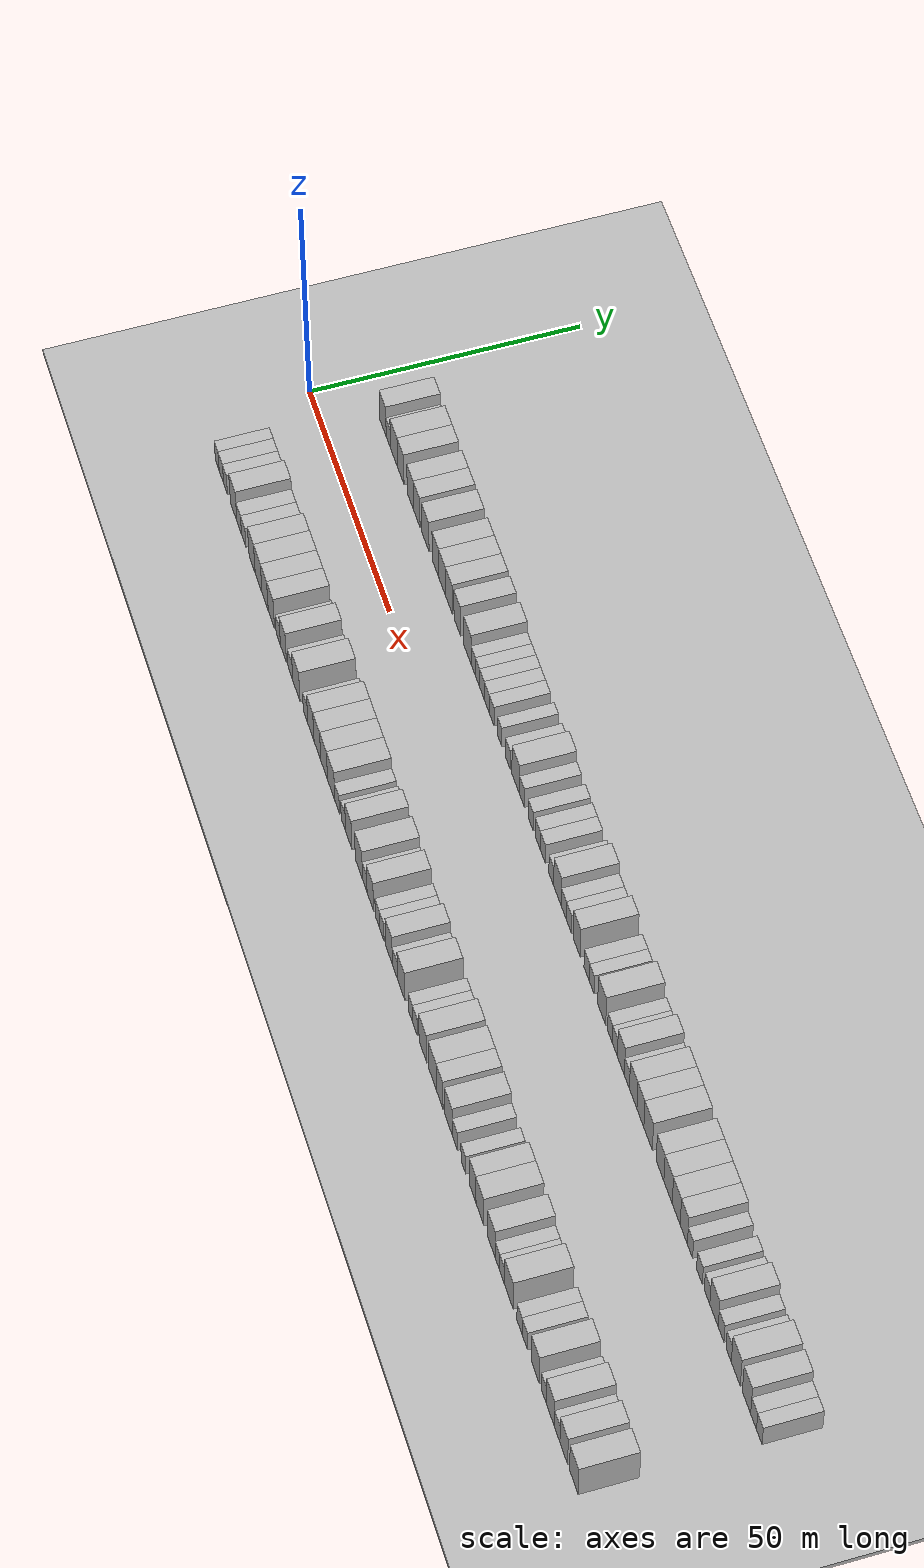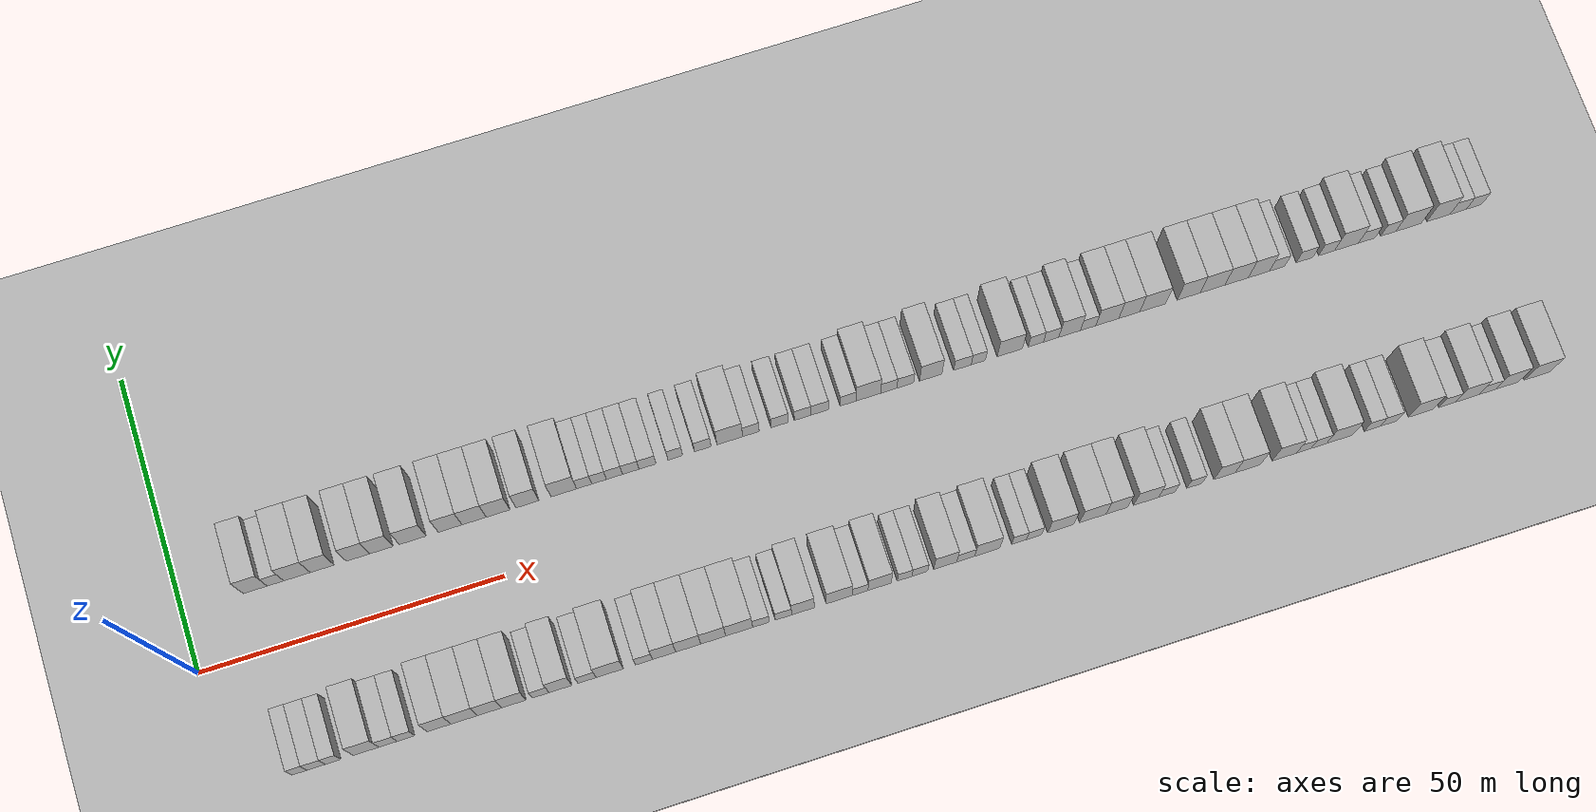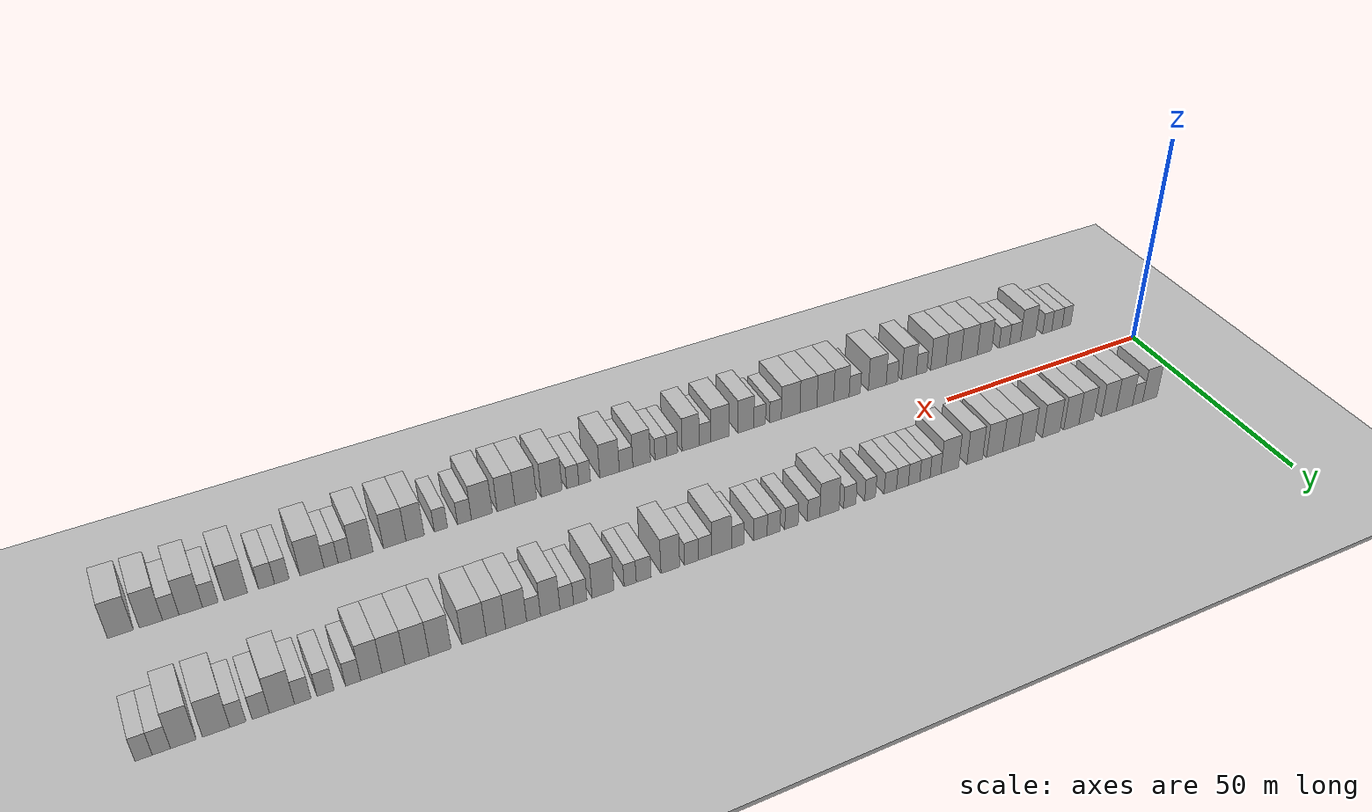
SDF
<?xml version="1.0" encoding="utf-8"?>

<sdf version="1.6">

   <world name="default">

      <gui fullscreen="0">

         <camera name="user_camera">

            <pose>-15 0 4.57585 0 0 0</pose>

            <view_controller>orbit</view_controller>

         </camera>

      </gui>

      <scene>

         <sky>

           <clouds>

             <speed>12</speed>

           </clouds>

         </sky>

         <ambient>0.4 0.4 0.4 1</ambient>

         <background>0.7 0.7 0.7 1</background>

         <shadows>1</shadows>

      </scene>

      <gravity>0 0 -9.8066</gravity>

      <magnetic_field>6e-06 2.3e-05 -4.2e-05</magnetic_field>

      <physics default="0" name="default_physics" type="ode">

         <ode>

            <solver>

               <type>quick</type>

               <iters>10</iters>

               <sor>1.0</sor>

               <use_dynamic_moi_rescaling>0</use_dynamic_moi_rescaling>

            </solver>

            <constraints>

               <cfm>0</cfm>

               <erp>0.2</erp>

               <contact_max_correcting_vel>100</contact_max_correcting_vel>

               <contact_surface_layer>0.001</contact_surface_layer>

            </constraints>

         </ode>

         <max_step_size>0.004</max_step_size>

         <real_time_factor>1</real_time_factor>

         <real_time_update_rate>250</real_time_update_rate>

      </physics>

      <light name="sun" type="directional">

         <cast_shadows>1</cast_shadows>

         <pose>0 0 10 0 0 0</pose>

         <diffuse>0.8 0.8 0.8 1</diffuse>

         <specular>0.2 0.2 0.2 1</specular>

         <attenuation>

            <range>1000</range>

            <constant>0.9</constant>

            <linear>0.01</linear>

            <quadratic>0.001</quadratic>

         </attenuation>

         <direction>-0.5 0.1 -0.9</direction>

      </light>

      <include>

         <name>ground_plane_1</name>

         <uri>model://HANNAS_ground_plane</uri>

         <pose>0 0 0  0 0 0</pose>

      </include>

      <include>

         <name>ground_plane_2</name>

         <uri>model://HANNAS_ground_plane</uri>

         <pose>100 0 0  0 0 0</pose>

      </include>

      <model name="building_1">

         <static>1</static>

         <pose frame="">11.9510 15.0000 0 0.000000 0.000000 1.570796</pose>

         <link name="link">

            <pose frame="">0 0 4.50 0 0 0</pose>

            <collision name="collision">

               <geometry>

                  <box>

                     <size>10.0000 3.9020 9.0000</size>

                  </box>

               </geometry>

               <max_contacts>10</max_contacts>

               <surface>

                  <contact>

                     <ode/>

                  </contact>

                  <bounce/>

                  <friction>

                     <torsional>

                        <ode/>

                     </torsional>

                     <ode/>

                  </friction>

               </surface>

            </collision>

            <visual name="visual">

               <cast_shadows>0</cast_shadows>

               <geometry>

                  <box>

                     <size>10.0000 3.9020 9.0000</size>

                  </box>

               </geometry>

               <material>

                  <script>

                     <uri>model://HANNAS_wall/materials/scripts</uri>

                     <uri>model://HANNAS_wall/materials/textures</uri>

                     <name>vrc/HANNAS_wall</name>

                  </script>

               </material>

            </visual>

            <self_collide>0</self_collide>

            <enable_wind>0</enable_wind>

            <kinematic>0</kinematic>

         </link>

      </model>

      <model name="building_2">

         <static>1</static>

         <pose frame="">15.2485 15.0000 0 0.000000 0.000000 1.570796</pose>

         <link name="link">

            <pose frame="">0 0 3.00 0 0 0</pose>

            <collision name="collision">

               <geometry>

                  <box>

                     <size>10.0000 2.6931 6.0000</size>

                  </box>

               </geometry>

               <max_contacts>10</max_contacts>

               <surface>

                  <contact>

                     <ode/>

                  </contact>

                  <bounce/>

                  <friction>

                     <torsional>

                        <ode/>

                     </torsional>

                     <ode/>

                  </friction>

               </surface>

            </collision>

            <visual name="visual">

               <cast_shadows>0</cast_shadows>

               <geometry>

                  <box>

                     <size>10.0000 2.6931 6.0000</size>

                  </box>

               </geometry>

               <material>

                  <script>

                     <uri>model://HANNAS_wall/materials/scripts</uri>

                     <uri>model://HANNAS_wall/materials/textures</uri>

                     <name>vrc/HANNAS_wall</name>

                  </script>

               </material>

            </visual>

            <self_collide>0</self_collide>

            <enable_wind>0</enable_wind>

            <kinematic>0</kinematic>

         </link>

      </model>

      <model name="building_3">

         <static>1</static>

         <pose frame="">18.7668 15.0000 0 0.000000 0.000000 1.570796</pose>

         <link name="link">

            <pose frame="">0 0 4.50 0 0 0</pose>

            <collision name="collision">

               <geometry>

                  <box>

                     <size>10.0000 4.3433 9.0000</size>

                  </box>

               </geometry>

               <max_contacts>10</max_contacts>

               <surface>

                  <contact>

                     <ode/>

                  </contact>

                  <bounce/>

                  <friction>

                     <torsional>

                        <ode/>

                     </torsional>

                     <ode/>

                  </friction>

               </surface>

            </collision>

            <visual name="visual">

               <cast_shadows>0</cast_shadows>

               <geometry>

                  <box>

                     <size>10.0000 4.3433 9.0000</size>

                  </box>

               </geometry>

               <material>

                  <script>

                     <uri>model://HANNAS_wall/materials/scripts</uri>

                     <uri>model://HANNAS_wall/materials/textures</uri>

                     <name>vrc/HANNAS_wall</name>

                  </script>

               </material>

            </visual>

            <self_collide>0</self_collide>

            <enable_wind>0</enable_wind>

            <kinematic>0</kinematic>

         </link>

      </model>

      <model name="building_4">

         <static>1</static>

         <pose frame="">22.8934 15.0000 0 0.000000 0.000000 1.570796</pose>

         <link name="link">

            <pose frame="">0 0 4.50 0 0 0</pose>

            <collision name="collision">

               <geometry>

                  <box>

                     <size>10.0000 3.9101 9.0000</size>

                  </box>

               </geometry>

               <max_contacts>10</max_contacts>

               <surface>

                  <contact>

                     <ode/>

                  </contact>

                  <bounce/>

                  <friction>

                     <torsional>

                        <ode/>

                     </torsional>

                     <ode/>

                  </friction>

               </surface>

            </collision>

            <visual name="visual">

               <cast_shadows>0</cast_shadows>

               <geometry>

                  <box>

                     <size>10.0000 3.9101 9.0000</size>

                  </box>

               </geometry>

               <material>

                  <script>

                     <uri>model://HANNAS_wall/materials/scripts</uri>

                     <uri>model://HANNAS_wall/materials/textures</uri>

                     <name>vrc/HANNAS_wall</name>

                  </script>

               </material>

            </visual>

            <self_collide>0</self_collide>

            <enable_wind>0</enable_wind>

            <kinematic>0</kinematic>

         </link>

      </model>

      <model name="building_5">

         <static>1</static>

         <pose frame="">28.7797 15.0000 0 0.000000 0.000000 1.570796</pose>

         <link name="link">

            <pose frame="">0 0 4.50 0 0 0</pose>

            <collision name="collision">

               <geometry>

                  <box>

                     <size>10.0000 3.8624 9.0000</size>

                  </box>

               </geometry>

               <max_contacts>10</max_contacts>

               <surface>

                  <contact>

                     <ode/>

                  </contact>

                  <bounce/>

                  <friction>

                     <torsional>

                        <ode/>

                     </torsional>

                     <ode/>

                  </friction>

               </surface>

            </collision>

            <visual name="visual">

               <cast_shadows>0</cast_shadows>

               <geometry>

                  <box>

                     <size>10.0000 3.8624 9.0000</size>

                  </box>

               </geometry>

               <material>

                  <script>

                     <uri>model://HANNAS_wall/materials/scripts</uri>

                     <uri>model://HANNAS_wall/materials/textures</uri>

                     <name>vrc/HANNAS_wall</name>

                  </script>

               </material>

            </visual>

            <self_collide>0</self_collide>

            <enable_wind>0</enable_wind>

            <kinematic>0</kinematic>

         </link>

      </model>

      <model name="building_6">

         <static>1</static>

         <pose frame="">32.6472 15.0000 0 0.000000 0.000000 1.570796</pose>

         <link name="link">

            <pose frame="">0 0 4.50 0 0 0</pose>

            <collision name="collision">

               <geometry>

                  <box>

                     <size>10.0000 3.8726 9.0000</size>

                  </box>

               </geometry>

               <max_contacts>10</max_contacts>

               <surface>

                  <contact>

                     <ode/>

                  </contact>

                  <bounce/>

                  <friction>

                     <torsional>

                        <ode/>

                     </torsional>

                     <ode/>

                  </friction>

               </surface>

            </collision>

            <visual name="visual">

               <cast_shadows>0</cast_shadows>

               <geometry>

                  <box>

                     <size>10.0000 3.8726 9.0000</size>

                  </box>

               </geometry>

               <material>

                  <script>

                     <uri>model://HANNAS_wall/materials/scripts</uri>

                     <uri>model://HANNAS_wall/materials/textures</uri>

                     <name>vrc/HANNAS_wall</name>

                  </script>

               </material>

            </visual>

            <self_collide>0</self_collide>

            <enable_wind>0</enable_wind>

            <kinematic>0</kinematic>

         </link>

      </model>

      <model name="building_7">

         <static>1</static>

         <pose frame="">37.7968 15.0000 0 0.000000 0.000000 1.570796</pose>

         <link name="link">

            <pose frame="">0 0 4.50 0 0 0</pose>

            <collision name="collision">

               <geometry>

                  <box>

                     <size>10.0000 4.4267 9.0000</size>

                  </box>

               </geometry>

               <max_contacts>10</max_contacts>

               <surface>

                  <contact>

                     <ode/>

                  </contact>

                  <bounce/>

                  <friction>

                     <torsional>

                        <ode/>

                     </torsional>

                     <ode/>

                  </friction>

               </surface>

            </collision>

            <visual name="visual">

               <cast_shadows>0</cast_shadows>

               <geometry>

                  <box>

                     <size>10.0000 4.4267 9.0000</size>

                  </box>

               </geometry>

               <material>

                  <script>

                     <uri>model://HANNAS_wall/materials/scripts</uri>

                     <uri>model://HANNAS_wall/materials/textures</uri>

                     <name>vrc/HANNAS_wall</name>

                  </script>

               </material>

            </visual>

            <self_collide>0</self_collide>

            <enable_wind>0</enable_wind>

            <kinematic>0</kinematic>

         </link>

      </model>

      <model name="building_8">

         <static>1</static>

         <pose frame="">43.9708 15.0000 0 0.000000 0.000000 1.570796</pose>

         <link name="link">

            <pose frame="">0 0 4.50 0 0 0</pose>

            <collision name="collision">

               <geometry>

                  <box>

                     <size>10.0000 3.9212 9.0000</size>

                  </box>

               </geometry>

               <max_contacts>10</max_contacts>

               <surface>

                  <contact>

                     <ode/>

                  </contact>

                  <bounce/>

                  <friction>

                     <torsional>

                        <ode/>

                     </torsional>

                     <ode/>

                  </friction>

               </surface>

            </collision>

            <visual name="visual">

               <cast_shadows>0</cast_shadows>

               <geometry>

                  <box>

                     <size>10.0000 3.9212 9.0000</size>

                  </box>

               </geometry>

               <material>

                  <script>

                     <uri>model://HANNAS_wall/materials/scripts</uri>

                     <uri>model://HANNAS_wall/materials/textures</uri>

                     <name>vrc/HANNAS_wall</name>

                  </script>

               </material>

            </visual>

            <self_collide>0</self_collide>

            <enable_wind>0</enable_wind>

            <kinematic>0</kinematic>

         </link>

      </model>

      <model name="building_9">

         <static>1</static>

         <pose frame="">47.9427 15.0000 0 0.000000 0.000000 1.570796</pose>

         <link name="link">

            <pose frame="">0 0 4.50 0 0 0</pose>

            <collision name="collision">

               <geometry>

                  <box>

                     <size>10.0000 4.0226 9.0000</size>

                  </box>

               </geometry>

               <max_contacts>10</max_contacts>

               <surface>

                  <contact>

                     <ode/>

                  </contact>

                  <bounce/>

                  <friction>

                     <torsional>

                        <ode/>

                     </torsional>

                     <ode/>

                  </friction>

               </surface>

            </collision>

            <visual name="visual">

               <cast_shadows>0</cast_shadows>

               <geometry>

                  <box>

                     <size>10.0000 4.0226 9.0000</size>

                  </box>

               </geometry>

               <material>

                  <script>

                     <uri>model://HANNAS_wall/materials/scripts</uri>

                     <uri>model://HANNAS_wall/materials/textures</uri>

                     <name>vrc/HANNAS_wall</name>

                  </script>

               </material>

            </visual>

            <self_collide>0</self_collide>

            <enable_wind>0</enable_wind>

            <kinematic>0</kinematic>

         </link>

      </model>

      <model name="building_10">

         <static>1</static>

         <pose frame="">51.9227 15.0000 0 0.000000 0.000000 1.570796</pose>

         <link name="link">

            <pose frame="">0 0 4.50 0 0 0</pose>

            <collision name="collision">

               <geometry>

                  <box>

                     <size>10.0000 3.9374 9.0000</size>

                  </box>

               </geometry>

               <max_contacts>10</max_contacts>

               <surface>

                  <contact>

                     <ode/>

                  </contact>

                  <bounce/>

                  <friction>

                     <torsional>

                        <ode/>

                     </torsional>

                     <ode/>

                  </friction>

               </surface>

            </collision>

            <visual name="visual">

               <cast_shadows>0</cast_shadows>

               <geometry>

                  <box>

                     <size>10.0000 3.9374 9.0000</size>

                  </box>

               </geometry>

               <material>

                  <script>

                     <uri>model://HANNAS_wall/materials/scripts</uri>

                     <uri>model://HANNAS_wall/materials/textures</uri>

                     <name>vrc/HANNAS_wall</name>

                  </script>

               </material>

            </visual>

            <self_collide>0</self_collide>

            <enable_wind>0</enable_wind>

            <kinematic>0</kinematic>

         </link>

      </model>

      <model name="building_11">

         <static>1</static>

         <pose frame="">56.7916 15.0000 0 0.000000 0.000000 1.570796</pose>

         <link name="link">

            <pose frame="">0 0 4.50 0 0 0</pose>

            <collision name="collision">

               <geometry>

                  <box>

                     <size>10.0000 3.8004 9.0000</size>

                  </box>

               </geometry>

               <max_contacts>10</max_contacts>

               <surface>

                  <contact>

                     <ode/>

                  </contact>

                  <bounce/>

                  <friction>

                     <torsional>

                        <ode/>

                     </torsional>

                     <ode/>

                  </friction>

               </surface>

            </collision>

            <visual name="visual">

               <cast_shadows>0</cast_shadows>

               <geometry>

                  <box>

                     <size>10.0000 3.8004 9.0000</size>

                  </box>

               </geometry>

               <material>

                  <script>

                     <uri>model://HANNAS_wall/materials/scripts</uri>

                     <uri>model://HANNAS_wall/materials/textures</uri>

                     <name>vrc/HANNAS_wall</name>

                  </script>

               </material>

            </visual>

            <self_collide>0</self_collide>

            <enable_wind>0</enable_wind>

            <kinematic>0</kinematic>

         </link>

      </model>

      <model name="building_12">

         <static>1</static>

         <pose frame="">62.8235 15.0000 0 0.000000 0.000000 1.570796</pose>

         <link name="link">

            <pose frame="">0 0 4.50 0 0 0</pose>

            <collision name="collision">

               <geometry>

                  <box>

                     <size>10.0000 4.2633 9.0000</size>

                  </box>

               </geometry>

               <max_contacts>10</max_contacts>

               <surface>

                  <contact>

                     <ode/>

                  </contact>

                  <bounce/>

                  <friction>

                     <torsional>

                        <ode/>

                     </torsional>

                     <ode/>

                  </friction>

               </surface>

            </collision>

            <visual name="visual">

               <cast_shadows>0</cast_shadows>

               <geometry>

                  <box>

                     <size>10.0000 4.2633 9.0000</size>

                  </box>

               </geometry>

               <material>

                  <script>

                     <uri>model://HANNAS_wall/materials/scripts</uri>

                     <uri>model://HANNAS_wall/materials/textures</uri>

                     <name>vrc/HANNAS_wall</name>

                  </script>

               </material>

            </visual>

            <self_collide>0</self_collide>

            <enable_wind>0</enable_wind>

            <kinematic>0</kinematic>

         </link>

      </model>

      <model name="building_13">

         <static>1</static>

         <pose frame="">66.2284 15.0000 0 0.000000 0.000000 1.570796</pose>

         <link name="link">

            <pose frame="">0 0 3.00 0 0 0</pose>

            <collision name="collision">

               <geometry>

                  <box>

                     <size>10.0000 2.5465 6.0000</size>

                  </box>

               </geometry>

               <max_contacts>10</max_contacts>

               <surface>

                  <contact>

                     <ode/>

                  </contact>

                  <bounce/>

                  <friction>

                     <torsional>

                        <ode/>

                     </torsional>

                     <ode/>

                  </friction>

               </surface>

            </collision>

            <visual name="visual">

               <cast_shadows>0</cast_shadows>

               <geometry>

                  <box>

                     <size>10.0000 2.5465 6.0000</size>

                  </box>

               </geometry>

               <material>

                  <script>

                     <uri>model://HANNAS_wall/materials/scripts</uri>

                     <uri>model://HANNAS_wall/materials/textures</uri>

                     <name>vrc/HANNAS_wall</name>

                  </script>

               </material>

            </visual>

            <self_collide>0</self_collide>

            <enable_wind>0</enable_wind>

            <kinematic>0</kinematic>

         </link>

      </model>

      <model name="building_14">

         <static>1</static>

         <pose frame="">68.7185 15.0000 0 0.000000 0.000000 1.570796</pose>

         <link name="link">

            <pose frame="">0 0 3.00 0 0 0</pose>

            <collision name="collision">

               <geometry>

                  <box>

                     <size>10.0000 2.4337 6.0000</size>

                  </box>

               </geometry>

               <max_contacts>10</max_contacts>

               <surface>

                  <contact>

                     <ode/>

                  </contact>

                  <bounce/>

                  <friction>

                     <torsional>

                        <ode/>

                     </torsional>

                     <ode/>

                  </friction>

               </surface>

            </collision>

            <visual name="visual">

               <cast_shadows>0</cast_shadows>

               <geometry>

                  <box>

                     <size>10.0000 2.4337 6.0000</size>

                  </box>

               </geometry>

               <material>

                  <script>

                     <uri>model://HANNAS_wall/materials/scripts</uri>

                     <uri>model://HANNAS_wall/materials/textures</uri>

                     <name>vrc/HANNAS_wall</name>

                  </script>

               </material>

            </visual>

            <self_collide>0</self_collide>

            <enable_wind>0</enable_wind>

            <kinematic>0</kinematic>

         </link>

      </model>

      <model name="building_15">

         <static>1</static>

         <pose frame="">71.2841 15.0000 0 0.000000 0.000000 1.570796</pose>

         <link name="link">

            <pose frame="">0 0 3.00 0 0 0</pose>

            <collision name="collision">

               <geometry>

                  <box>

                     <size>10.0000 2.6976 6.0000</size>

                  </box>

               </geometry>

               <max_contacts>10</max_contacts>

               <surface>

                  <contact>

                     <ode/>

                  </contact>

                  <bounce/>

                  <friction>

                     <torsional>

                        <ode/>

                     </torsional>

                     <ode/>

                  </friction>

               </surface>

            </collision>

            <visual name="visual">

               <cast_shadows>0</cast_shadows>

               <geometry>

                  <box>

                     <size>10.0000 2.6976 6.0000</size>

                  </box>

               </geometry>

               <material>

                  <script>

                     <uri>model://HANNAS_wall/materials/scripts</uri>

                     <uri>model://HANNAS_wall/materials/textures</uri>

                     <name>vrc/HANNAS_wall</name>

                  </script>

               </material>

            </visual>

            <self_collide>0</self_collide>

            <enable_wind>0</enable_wind>

            <kinematic>0</kinematic>

         </link>

      </model>

      <model name="building_16">

         <static>1</static>

         <pose frame="">74.0103 15.0000 0 0.000000 0.000000 1.570796</pose>

         <link name="link">

            <pose frame="">0 0 3.00 0 0 0</pose>

            <collision name="collision">

               <geometry>

                  <box>

                     <size>10.0000 2.7549 6.0000</size>

                  </box>

               </geometry>

               <max_contacts>10</max_contacts>

               <surface>

                  <contact>

                     <ode/>

                  </contact>

                  <bounce/>

                  <friction>

                     <torsional>

                        <ode/>

                     </torsional>

                     <ode/>

                  </friction>

               </surface>

            </collision>

            <visual name="visual">

               <cast_shadows>0</cast_shadows>

               <geometry>

                  <box>

                     <size>10.0000 2.7549 6.0000</size>

                  </box>

               </geometry>

               <material>

                  <script>

                     <uri>model://HANNAS_wall/materials/scripts</uri>

                     <uri>model://HANNAS_wall/materials/textures</uri>

                     <name>vrc/HANNAS_wall</name>

                  </script>

               </material>

            </visual>

            <self_collide>0</self_collide>

            <enable_wind>0</enable_wind>

            <kinematic>0</kinematic>

         </link>

      </model>

      <model name="building_17">

         <static>1</static>

         <pose frame="">76.8111 15.0000 0 0.000000 0.000000 1.570796</pose>

         <link name="link">

            <pose frame="">0 0 3.00 0 0 0</pose>

            <collision name="collision">

               <geometry>

                  <box>

                     <size>10.0000 2.8467 6.0000</size>

                  </box>

               </geometry>

               <max_contacts>10</max_contacts>

               <surface>

                  <contact>

                     <ode/>

                  </contact>

                  <bounce/>

                  <friction>

                     <torsional>

                        <ode/>

                     </torsional>

                     <ode/>

                  </friction>

               </surface>

            </collision>

            <visual name="visual">

               <cast_shadows>0</cast_shadows>

               <geometry>

                  <box>

                     <size>10.0000 2.8467 6.0000</size>

                  </box>

               </geometry>

               <material>

                  <script>

                     <uri>model://HANNAS_wall/materials/scripts</uri>

                     <uri>model://HANNAS_wall/materials/textures</uri>

                     <name>vrc/HANNAS_wall</name>

                  </script>

               </material>

            </visual>

            <self_collide>0</self_collide>

            <enable_wind>0</enable_wind>

            <kinematic>0</kinematic>

         </link>

      </model>

      <model name="building_18">

         <static>1</static>

         <pose frame="">81.4646 15.0000 0 0.000000 0.000000 1.570796</pose>

         <link name="link">

            <pose frame="">0 0 3.00 0 0 0</pose>

            <collision name="collision">

               <geometry>

                  <box>

                     <size>10.0000 2.4603 6.0000</size>

                  </box>

               </geometry>

               <max_contacts>10</max_contacts>

               <surface>

                  <contact>

                     <ode/>

                  </contact>

                  <bounce/>

                  <friction>

                     <torsional>

                        <ode/>

                     </torsional>

                     <ode/>

                  </friction>

               </surface>

            </collision>

            <visual name="visual">

               <cast_shadows>0</cast_shadows>

               <geometry>

                  <box>

                     <size>10.0000 2.4603 6.0000</size>

                  </box>

               </geometry>

               <material>

                  <script>

                     <uri>model://HANNAS_wall/materials/scripts</uri>

                     <uri>model://HANNAS_wall/materials/textures</uri>

                     <name>vrc/HANNAS_wall</name>

                  </script>

               </material>

            </visual>

            <self_collide>0</self_collide>

            <enable_wind>0</enable_wind>

            <kinematic>0</kinematic>

         </link>

      </model>

      <model name="building_19">

         <static>1</static>

         <pose frame="">86.0817 15.0000 0 0.000000 0.000000 1.570796</pose>

         <link name="link">

            <pose frame="">0 0 3.00 0 0 0</pose>

            <collision name="collision">

               <geometry>

                  <box>

                     <size>10.0000 2.7739 6.0000</size>

                  </box>

               </geometry>

               <max_contacts>10</max_contacts>

               <surface>

                  <contact>

                     <ode/>

                  </contact>

                  <bounce/>

                  <friction>

                     <torsional>

                        <ode/>

                     </torsional>

                     <ode/>

                  </friction>

               </surface>

            </collision>

            <visual name="visual">

               <cast_shadows>0</cast_shadows>

               <geometry>

                  <box>

                     <size>10.0000 2.7739 6.0000</size>

                  </box>

               </geometry>

               <material>

                  <script>

                     <uri>model://HANNAS_wall/materials/scripts</uri>

                     <uri>model://HANNAS_wall/materials/textures</uri>

                     <name>vrc/HANNAS_wall</name>

                  </script>

               </material>

            </visual>

            <self_collide>0</self_collide>

            <enable_wind>0</enable_wind>

            <kinematic>0</kinematic>

         </link>

      </model>

      <model name="building_20">

         <static>1</static>

         <pose frame="">90.6306 15.0000 0 0.000000 0.000000 1.570796</pose>

         <link name="link">

            <pose frame="">0 0 4.50 0 0 0</pose>

            <collision name="collision">

               <geometry>

                  <box>

                     <size>10.0000 4.3240 9.0000</size>

                  </box>

               </geometry>

               <max_contacts>10</max_contacts>

               <surface>

                  <contact>

                     <ode/>

                  </contact>

                  <bounce/>

                  <friction>

                     <torsional>

                        <ode/>

                     </torsional>

                     <ode/>

                  </friction>

               </surface>

            </collision>

            <visual name="visual">

               <cast_shadows>0</cast_shadows>

               <geometry>

                  <box>

                     <size>10.0000 4.3240 9.0000</size>

                  </box>

               </geometry>

               <material>

                  <script>

                     <uri>model://HANNAS_wall/materials/scripts</uri>

                     <uri>model://HANNAS_wall/materials/textures</uri>

                     <name>vrc/HANNAS_wall</name>

                  </script>

               </material>

            </visual>

            <self_collide>0</self_collide>

            <enable_wind>0</enable_wind>

            <kinematic>0</kinematic>

         </link>

      </model>

      <model name="building_21">

         <static>1</static>

         <pose frame="">94.1818 15.0000 0 0.000000 0.000000 1.570796</pose>

         <link name="link">

            <pose frame="">0 0 3.00 0 0 0</pose>

            <collision name="collision">

               <geometry>

                  <box>

                     <size>10.0000 2.7784 6.0000</size>

                  </box>

               </geometry>

               <max_contacts>10</max_contacts>

               <surface>

                  <contact>

                     <ode/>

                  </contact>

                  <bounce/>

                  <friction>

                     <torsional>

                        <ode/>

                     </torsional>

                     <ode/>

                  </friction>

               </surface>

            </collision>

            <visual name="visual">

               <cast_shadows>0</cast_shadows>

               <geometry>

                  <box>

                     <size>10.0000 2.7784 6.0000</size>

                  </box>

               </geometry>

               <material>

                  <script>

                     <uri>model://HANNAS_wall/materials/scripts</uri>

                     <uri>model://HANNAS_wall/materials/textures</uri>

                     <name>vrc/HANNAS_wall</name>

                  </script>

               </material>

            </visual>

            <self_collide>0</self_collide>

            <enable_wind>0</enable_wind>

            <kinematic>0</kinematic>

         </link>

      </model>

      <model name="building_22">

         <static>1</static>

         <pose frame="">99.0298 15.0000 0 0.000000 0.000000 1.570796</pose>

         <link name="link">

            <pose frame="">0 0 3.00 0 0 0</pose>

            <collision name="collision">

               <geometry>

                  <box>

                     <size>10.0000 2.9176 6.0000</size>

                  </box>

               </geometry>

               <max_contacts>10</max_contacts>

               <surface>

                  <contact>

                     <ode/>

                  </contact>

                  <bounce/>

                  <friction>

                     <torsional>

                        <ode/>

                     </torsional>

                     <ode/>

                  </friction>

               </surface>

            </collision>

            <visual name="visual">

               <cast_shadows>0</cast_shadows>

               <geometry>

                  <box>

                     <size>10.0000 2.9176 6.0000</size>

                  </box>

               </geometry>

               <material>

                  <script>

                     <uri>model://HANNAS_wall/materials/scripts</uri>

                     <uri>model://HANNAS_wall/materials/textures</uri>

                     <name>vrc/HANNAS_wall</name>

                  </script>

               </material>

            </visual>

            <self_collide>0</self_collide>

            <enable_wind>0</enable_wind>

            <kinematic>0</kinematic>

         </link>

      </model>

      <model name="building_23">

         <static>1</static>

         <pose frame="">102.8933 15.0000 0 0.000000 0.000000 1.570796</pose>

         <link name="link">

            <pose frame="">0 0 3.00 0 0 0</pose>

            <collision name="collision">

               <geometry>

                  <box>

                     <size>10.0000 2.8093 6.0000</size>

                  </box>

               </geometry>

               <max_contacts>10</max_contacts>

               <surface>

                  <contact>

                     <ode/>

                  </contact>

                  <bounce/>

                  <friction>

                     <torsional>

                        <ode/>

                     </torsional>

                     <ode/>

                  </friction>

               </surface>

            </collision>

            <visual name="visual">

               <cast_shadows>0</cast_shadows>

               <geometry>

                  <box>

                     <size>10.0000 2.8093 6.0000</size>

                  </box>

               </geometry>

               <material>

                  <script>

                     <uri>model://HANNAS_wall/materials/scripts</uri>

                     <uri>model://HANNAS_wall/materials/textures</uri>

                     <name>vrc/HANNAS_wall</name>

                  </script>

               </material>

            </visual>

            <self_collide>0</self_collide>

            <enable_wind>0</enable_wind>

            <kinematic>0</kinematic>

         </link>

      </model>

      <model name="building_24">

         <static>1</static>

         <pose frame="">105.7759 15.0000 0 0.000000 0.000000 1.570796</pose>

         <link name="link">

            <pose frame="">0 0 3.00 0 0 0</pose>

            <collision name="collision">

               <geometry>

                  <box>

                     <size>10.0000 2.9560 6.0000</size>

                  </box>

               </geometry>

               <max_contacts>10</max_contacts>

               <surface>

                  <contact>

                     <ode/>

                  </contact>

                  <bounce/>

                  <friction>

                     <torsional>

                        <ode/>

                     </torsional>

                     <ode/>

                  </friction>

               </surface>

            </collision>

            <visual name="visual">

               <cast_shadows>0</cast_shadows>

               <geometry>

                  <box>

                     <size>10.0000 2.9560 6.0000</size>

                  </box>

               </geometry>

               <material>

                  <script>

                     <uri>model://HANNAS_wall/materials/scripts</uri>

                     <uri>model://HANNAS_wall/materials/textures</uri>

                     <name>vrc/HANNAS_wall</name>

                  </script>

               </material>

            </visual>

            <self_collide>0</self_collide>

            <enable_wind>0</enable_wind>

            <kinematic>0</kinematic>

         </link>

      </model>

      <model name="building_25">

         <static>1</static>

         <pose frame="">110.5981 15.0000 0 0.000000 0.000000 1.570796</pose>

         <link name="link">

            <pose frame="">0 0 3.00 0 0 0</pose>

            <collision name="collision">

               <geometry>

                  <box>

                     <size>10.0000 2.6883 6.0000</size>

                  </box>

               </geometry>

               <max_contacts>10</max_contacts>

               <surface>

                  <contact>

                     <ode/>

                  </contact>

                  <bounce/>

                  <friction>

                     <torsional>

                        <ode/>

                     </torsional>

                     <ode/>

                  </friction>

               </surface>

            </collision>

            <visual name="visual">

               <cast_shadows>0</cast_shadows>

               <geometry>

                  <box>

                     <size>10.0000 2.6883 6.0000</size>

                  </box>

               </geometry>

               <material>

                  <script>

                     <uri>model://HANNAS_wall/materials/scripts</uri>

                     <uri>model://HANNAS_wall/materials/textures</uri>

                     <name>vrc/HANNAS_wall</name>

                  </script>

               </material>

            </visual>

            <self_collide>0</self_collide>

            <enable_wind>0</enable_wind>

            <kinematic>0</kinematic>

         </link>

      </model>

      <model name="building_26">

         <static>1</static>

         <pose frame="">114.0285 15.0000 0 0.000000 0.000000 1.570796</pose>

         <link name="link">

            <pose frame="">0 0 4.50 0 0 0</pose>

            <collision name="collision">

               <geometry>

                  <box>

                     <size>10.0000 4.1726 9.0000</size>

                  </box>

               </geometry>

               <max_contacts>10</max_contacts>

               <surface>

                  <contact>

                     <ode/>

                  </contact>

                  <bounce/>

                  <friction>

                     <torsional>

                        <ode/>

                     </torsional>

                     <ode/>

                  </friction>

               </surface>

            </collision>

            <visual name="visual">

               <cast_shadows>0</cast_shadows>

               <geometry>

                  <box>

                     <size>10.0000 4.1726 9.0000</size>

                  </box>

               </geometry>

               <material>

                  <script>

                     <uri>model://HANNAS_wall/materials/scripts</uri>

                     <uri>model://HANNAS_wall/materials/textures</uri>

                     <name>vrc/HANNAS_wall</name>

                  </script>

               </material>

            </visual>

            <self_collide>0</self_collide>

            <enable_wind>0</enable_wind>

            <kinematic>0</kinematic>

         </link>

      </model>

      <model name="building_27">

         <static>1</static>

         <pose frame="">117.4972 15.0000 0 0.000000 0.000000 1.570796</pose>

         <link name="link">

            <pose frame="">0 0 3.00 0 0 0</pose>

            <collision name="collision">

               <geometry>

                  <box>

                     <size>10.0000 2.7647 6.0000</size>

                  </box>

               </geometry>

               <max_contacts>10</max_contacts>

               <surface>

                  <contact>

                     <ode/>

                  </contact>

                  <bounce/>

                  <friction>

                     <torsional>

                        <ode/>

                     </torsional>

                     <ode/>

                  </friction>

               </surface>

            </collision>

            <visual name="visual">

               <cast_shadows>0</cast_shadows>

               <geometry>

                  <box>

                     <size>10.0000 2.7647 6.0000</size>

                  </box>

               </geometry>

               <material>

                  <script>

                     <uri>model://HANNAS_wall/materials/scripts</uri>

                     <uri>model://HANNAS_wall/materials/textures</uri>

                     <name>vrc/HANNAS_wall</name>

                  </script>

               </material>

            </visual>

            <self_collide>0</self_collide>

            <enable_wind>0</enable_wind>

            <kinematic>0</kinematic>

         </link>

      </model>

      <model name="building_28">

         <static>1</static>

         <pose frame="">120.3044 15.0000 0 0.000000 0.000000 1.570796</pose>

         <link name="link">

            <pose frame="">0 0 3.00 0 0 0</pose>

            <collision name="collision">

               <geometry>

                  <box>

                     <size>10.0000 2.8498 6.0000</size>

                  </box>

               </geometry>

               <max_contacts>10</max_contacts>

               <surface>

                  <contact>

                     <ode/>

                  </contact>

                  <bounce/>

                  <friction>

                     <torsional>

                        <ode/>

                     </torsional>

                     <ode/>

                  </friction>

               </surface>

            </collision>

            <visual name="visual">

               <cast_shadows>0</cast_shadows>

               <geometry>

                  <box>

                     <size>10.0000 2.8498 6.0000</size>

                  </box>

               </geometry>

               <material>

                  <script>

                     <uri>model://HANNAS_wall/materials/scripts</uri>

                     <uri>model://HANNAS_wall/materials/textures</uri>

                     <name>vrc/HANNAS_wall</name>

                  </script>

               </material>

            </visual>

            <self_collide>0</self_collide>

            <enable_wind>0</enable_wind>

            <kinematic>0</kinematic>

         </link>

      </model>

      <model name="building_29">

         <static>1</static>

         <pose frame="">124.6412 15.0000 0 0.000000 0.000000 1.570796</pose>

         <link name="link">

            <pose frame="">0 0 4.50 0 0 0</pose>

            <collision name="collision">

               <geometry>

                  <box>

                     <size>10.0000 3.8238 9.0000</size>

                  </box>

               </geometry>

               <max_contacts>10</max_contacts>

               <surface>

                  <contact>

                     <ode/>

                  </contact>

                  <bounce/>

                  <friction>

                     <torsional>

                        <ode/>

                     </torsional>

                     <ode/>

                  </friction>

               </surface>

            </collision>

            <visual name="visual">

               <cast_shadows>0</cast_shadows>

               <geometry>

                  <box>

                     <size>10.0000 3.8238 9.0000</size>

                  </box>

               </geometry>

               <material>

                  <script>

                     <uri>model://HANNAS_wall/materials/scripts</uri>

                     <uri>model://HANNAS_wall/materials/textures</uri>

                     <name>vrc/HANNAS_wall</name>

                  </script>

               </material>

            </visual>

            <self_collide>0</self_collide>

            <enable_wind>0</enable_wind>

            <kinematic>0</kinematic>

         </link>

      </model>

      <model name="building_30">

         <static>1</static>

         <pose frame="">130.0515 15.0000 0 0.000000 0.000000 1.570796</pose>

         <link name="link">

            <pose frame="">0 0 3.00 0 0 0</pose>

            <collision name="collision">

               <geometry>

                  <box>

                     <size>10.0000 2.9967 6.0000</size>

                  </box>

               </geometry>

               <max_contacts>10</max_contacts>

               <surface>

                  <contact>

                     <ode/>

                  </contact>

                  <bounce/>

                  <friction>

                     <torsional>

                        <ode/>

                     </torsional>

                     <ode/>

                  </friction>

               </surface>

            </collision>

            <visual name="visual">

               <cast_shadows>0</cast_shadows>

               <geometry>

                  <box>

                     <size>10.0000 2.9967 6.0000</size>

                  </box>

               </geometry>

               <material>

                  <script>

                     <uri>model://HANNAS_wall/materials/scripts</uri>

                     <uri>model://HANNAS_wall/materials/textures</uri>

                     <name>vrc/HANNAS_wall</name>

                  </script>

               </material>

            </visual>

            <self_collide>0</self_collide>

            <enable_wind>0</enable_wind>

            <kinematic>0</kinematic>

         </link>

      </model>

      <model name="building_31">

         <static>1</static>

         <pose frame="">132.7683 15.0000 0 0.000000 0.000000 1.570796</pose>

         <link name="link">

            <pose frame="">0 0 3.00 0 0 0</pose>

            <collision name="collision">

               <geometry>

                  <box>

                     <size>10.0000 2.4370 6.0000</size>

                  </box>

               </geometry>

               <max_contacts>10</max_contacts>

               <surface>

                  <contact>

                     <ode/>

                  </contact>

                  <bounce/>

                  <friction>

                     <torsional>

                        <ode/>

                     </torsional>

                     <ode/>

                  </friction>

               </surface>

            </collision>

            <visual name="visual">

               <cast_shadows>0</cast_shadows>

               <geometry>

                  <box>

                     <size>10.0000 2.4370 6.0000</size>

                  </box>

               </geometry>

               <material>

                  <script>

                     <uri>model://HANNAS_wall/materials/scripts</uri>

                     <uri>model://HANNAS_wall/materials/textures</uri>

                     <name>vrc/HANNAS_wall</name>

                  </script>

               </material>

            </visual>

            <self_collide>0</self_collide>

            <enable_wind>0</enable_wind>

            <kinematic>0</kinematic>

         </link>

      </model>

      <model name="building_32">

         <static>1</static>

         <pose frame="">138.1511 15.0000 0 0.000000 0.000000 1.570796</pose>

         <link name="link">

            <pose frame="">0 0 4.50 0 0 0</pose>

            <collision name="collision">

               <geometry>

                  <box>

                     <size>10.0000 4.3286 9.0000</size>

                  </box>

               </geometry>

               <max_contacts>10</max_contacts>

               <surface>

                  <contact>

                     <ode/>

                  </contact>

                  <bounce/>

                  <friction>

                     <torsional>

                        <ode/>

                     </torsional>

                     <ode/>

                  </friction>

               </surface>

            </collision>

            <visual name="visual">

               <cast_shadows>0</cast_shadows>

               <geometry>

                  <box>

                     <size>10.0000 4.3286 9.0000</size>

                  </box>

               </geometry>

               <material>

                  <script>

                     <uri>model://HANNAS_wall/materials/scripts</uri>

                     <uri>model://HANNAS_wall/materials/textures</uri>

                     <name>vrc/HANNAS_wall</name>

                  </script>

               </material>

            </visual>

            <self_collide>0</self_collide>

            <enable_wind>0</enable_wind>

            <kinematic>0</kinematic>

         </link>

      </model>

      <model name="building_33">

         <static>1</static>

         <pose frame="">142.6161 15.0000 0 0.000000 0.000000 1.570796</pose>

         <link name="link">

            <pose frame="">0 0 3.00 0 0 0</pose>

            <collision name="collision">

               <geometry>

                  <box>

                     <size>10.0000 2.6014 6.0000</size>

                  </box>

               </geometry>

               <max_contacts>10</max_contacts>

               <surface>

                  <contact>

                     <ode/>

                  </contact>

                  <bounce/>

                  <friction>

                     <torsional>

                        <ode/>

                     </torsional>

                     <ode/>

                  </friction>

               </surface>

            </collision>

            <visual name="visual">

               <cast_shadows>0</cast_shadows>

               <geometry>

                  <box>

                     <size>10.0000 2.6014 6.0000</size>

                  </box>

               </geometry>

               <material>

                  <script>

                     <uri>model://HANNAS_wall/materials/scripts</uri>

                     <uri>model://HANNAS_wall/materials/textures</uri>

                     <name>vrc/HANNAS_wall</name>

                  </script>

               </material>

            </visual>

            <self_collide>0</self_collide>

            <enable_wind>0</enable_wind>

            <kinematic>0</kinematic>

         </link>

      </model>

      <model name="building_34">

         <static>1</static>

         <pose frame="">145.2436 15.0000 0 0.000000 0.000000 1.570796</pose>

         <link name="link">

            <pose frame="">0 0 3.00 0 0 0</pose>

            <collision name="collision">

               <geometry>

                  <box>

                     <size>10.0000 2.6535 6.0000</size>

                  </box>

               </geometry>

               <max_contacts>10</max_contacts>

               <surface>

                  <contact>

                     <ode/>

                  </contact>

                  <bounce/>

                  <friction>

                     <torsional>

                        <ode/>

                     </torsional>

                     <ode/>

                  </friction>

               </surface>

            </collision>

            <visual name="visual">

               <cast_shadows>0</cast_shadows>

               <geometry>

                  <box>

                     <size>10.0000 2.6535 6.0000</size>

                  </box>

               </geometry>

               <material>

                  <script>

                     <uri>model://HANNAS_wall/materials/scripts</uri>

                     <uri>model://HANNAS_wall/materials/textures</uri>

                     <name>vrc/HANNAS_wall</name>

                  </script>

               </material>

            </visual>

            <self_collide>0</self_collide>

            <enable_wind>0</enable_wind>

            <kinematic>0</kinematic>

         </link>

      </model>

      <model name="building_35">

         <static>1</static>

         <pose frame="">148.4332 15.0000 0 0.000000 0.000000 1.570796</pose>

         <link name="link">

            <pose frame="">0 0 4.50 0 0 0</pose>

            <collision name="collision">

               <geometry>

                  <box>

                     <size>10.0000 3.7258 9.0000</size>

                  </box>

               </geometry>

               <max_contacts>10</max_contacts>

               <surface>

                  <contact>

                     <ode/>

                  </contact>

                  <bounce/>

                  <friction>

                     <torsional>

                        <ode/>

                     </torsional>

                     <ode/>

                  </friction>

               </surface>

            </collision>

            <visual name="visual">

               <cast_shadows>0</cast_shadows>

               <geometry>

                  <box>

                     <size>10.0000 3.7258 9.0000</size>

                  </box>

               </geometry>

               <material>

                  <script>

                     <uri>model://HANNAS_wall/materials/scripts</uri>

                     <uri>model://HANNAS_wall/materials/textures</uri>

                     <name>vrc/HANNAS_wall</name>

                  </script>

               </material>

            </visual>

            <self_collide>0</self_collide>

            <enable_wind>0</enable_wind>

            <kinematic>0</kinematic>

         </link>

      </model>

      <model name="building_36">

         <static>1</static>

         <pose frame="">151.6295 15.0000 0 0.000000 0.000000 1.570796</pose>

         <link name="link">

            <pose frame="">0 0 3.00 0 0 0</pose>

            <collision name="collision">

               <geometry>

                  <box>

                     <size>10.0000 2.6668 6.0000</size>

                  </box>

               </geometry>

               <max_contacts>10</max_contacts>

               <surface>

                  <contact>

                     <ode/>

                  </contact>

                  <bounce/>

                  <friction>

                     <torsional>

                        <ode/>

                     </torsional>

                     <ode/>

                  </friction>

               </surface>

            </collision>

            <visual name="visual">

               <cast_shadows>0</cast_shadows>

               <geometry>

                  <box>

                     <size>10.0000 2.6668 6.0000</size>

                  </box>

               </geometry>

               <material>

                  <script>

                     <uri>model://HANNAS_wall/materials/scripts</uri>

                     <uri>model://HANNAS_wall/materials/textures</uri>

                     <name>vrc/HANNAS_wall</name>

                  </script>

               </material>

            </visual>

            <self_collide>0</self_collide>

            <enable_wind>0</enable_wind>

            <kinematic>0</kinematic>

         </link>

      </model>

      <model name="building_37">

         <static>1</static>

         <pose frame="">154.9333 15.0000 0 0.000000 0.000000 1.570796</pose>

         <link name="link">

            <pose frame="">0 0 4.50 0 0 0</pose>

            <collision name="collision">

               <geometry>

                  <box>

                     <size>10.0000 3.9408 9.0000</size>

                  </box>

               </geometry>

               <max_contacts>10</max_contacts>

               <surface>

                  <contact>

                     <ode/>

                  </contact>

                  <bounce/>

                  <friction>

                     <torsional>

                        <ode/>

                     </torsional>

                     <ode/>

                  </friction>

               </surface>

            </collision>

            <visual name="visual">

               <cast_shadows>0</cast_shadows>

               <geometry>

                  <box>

                     <size>10.0000 3.9408 9.0000</size>

                  </box>

               </geometry>

               <material>

                  <script>

                     <uri>model://HANNAS_wall/materials/scripts</uri>

                     <uri>model://HANNAS_wall/materials/textures</uri>

                     <name>vrc/HANNAS_wall</name>

                  </script>

               </material>

            </visual>

            <self_collide>0</self_collide>

            <enable_wind>0</enable_wind>

            <kinematic>0</kinematic>

         </link>

      </model>

      <model name="building_38">

         <static>1</static>

         <pose frame="">158.7264 15.0000 0 0.000000 0.000000 1.570796</pose>

         <link name="link">

            <pose frame="">0 0 4.50 0 0 0</pose>

            <collision name="collision">

               <geometry>

                  <box>

                     <size>10.0000 3.6454 9.0000</size>

                  </box>

               </geometry>

               <max_contacts>10</max_contacts>

               <surface>

                  <contact>

                     <ode/>

                  </contact>

                  <bounce/>

                  <friction>

                     <torsional>

                        <ode/>

                     </torsional>

                     <ode/>

                  </friction>

               </surface>

            </collision>

            <visual name="visual">

               <cast_shadows>0</cast_shadows>

               <geometry>

                  <box>

                     <size>10.0000 3.6454 9.0000</size>

                  </box>

               </geometry>

               <material>

                  <script>

                     <uri>model://HANNAS_wall/materials/scripts</uri>

                     <uri>model://HANNAS_wall/materials/textures</uri>

                     <name>vrc/HANNAS_wall</name>

                  </script>

               </material>

            </visual>

            <self_collide>0</self_collide>

            <enable_wind>0</enable_wind>

            <kinematic>0</kinematic>

         </link>

      </model>

      <model name="building_39">

         <static>1</static>

         <pose frame="">162.7712 15.0000 0 0.000000 0.000000 1.570796</pose>

         <link name="link">

            <pose frame="">0 0 4.50 0 0 0</pose>

            <collision name="collision">

               <geometry>

                  <box>

                     <size>10.0000 4.4442 9.0000</size>

                  </box>

               </geometry>

               <max_contacts>10</max_contacts>

               <surface>

                  <contact>

                     <ode/>

                  </contact>

                  <bounce/>

                  <friction>

                     <torsional>

                        <ode/>

                     </torsional>

                     <ode/>

                  </friction>

               </surface>

            </collision>

            <visual name="visual">

               <cast_shadows>0</cast_shadows>

               <geometry>

                  <box>

                     <size>10.0000 4.4442 9.0000</size>

                  </box>

               </geometry>

               <material>

                  <script>

                     <uri>model://HANNAS_wall/materials/scripts</uri>

                     <uri>model://HANNAS_wall/materials/textures</uri>

                     <name>vrc/HANNAS_wall</name>

                  </script>

               </material>

            </visual>

            <self_collide>0</self_collide>

            <enable_wind>0</enable_wind>

            <kinematic>0</kinematic>

         </link>

      </model>

      <model name="building_40">

         <static>1</static>

         <pose frame="">168.9857 15.0000 0 0.000000 0.000000 1.570796</pose>

         <link name="link">

            <pose frame="">0 0 4.50 0 0 0</pose>

            <collision name="collision">

               <geometry>

                  <box>

                     <size>10.0000 3.9849 9.0000</size>

                  </box>

               </geometry>

               <max_contacts>10</max_contacts>

               <surface>

                  <contact>

                     <ode/>

                  </contact>

                  <bounce/>

                  <friction>

                     <torsional>

                        <ode/>

                     </torsional>

                     <ode/>

                  </friction>

               </surface>

            </collision>

            <visual name="visual">

               <cast_shadows>0</cast_shadows>

               <geometry>

                  <box>

                     <size>10.0000 3.9849 9.0000</size>

                  </box>

               </geometry>

               <material>

                  <script>

                     <uri>model://HANNAS_wall/materials/scripts</uri>

                     <uri>model://HANNAS_wall/materials/textures</uri>

                     <name>vrc/HANNAS_wall</name>

                  </script>

               </material>

            </visual>

            <self_collide>0</self_collide>

            <enable_wind>0</enable_wind>

            <kinematic>0</kinematic>

         </link>

      </model>

      <model name="building_41">

         <static>1</static>

         <pose frame="">173.1314 15.0000 0 0.000000 0.000000 1.570796</pose>

         <link name="link">

            <pose frame="">0 0 4.50 0 0 0</pose>

            <collision name="collision">

               <geometry>

                  <box>

                     <size>10.0000 4.3065 9.0000</size>

                  </box>

               </geometry>

               <max_contacts>10</max_contacts>

               <surface>

                  <contact>

                     <ode/>

                  </contact>

                  <bounce/>

                  <friction>

                     <torsional>

                        <ode/>

                     </torsional>

                     <ode/>

                  </friction>

               </surface>

            </collision>

            <visual name="visual">

               <cast_shadows>0</cast_shadows>

               <geometry>

                  <box>

                     <size>10.0000 4.3065 9.0000</size>

                  </box>

               </geometry>

               <material>

                  <script>

                     <uri>model://HANNAS_wall/materials/scripts</uri>

                     <uri>model://HANNAS_wall/materials/textures</uri>

                     <name>vrc/HANNAS_wall</name>

                  </script>

               </material>

            </visual>

            <self_collide>0</self_collide>

            <enable_wind>0</enable_wind>

            <kinematic>0</kinematic>

         </link>

      </model>

      <model name="building_42">

         <static>1</static>

         <pose frame="">177.3272 15.0000 0 0.000000 0.000000 1.570796</pose>

         <link name="link">

            <pose frame="">0 0 4.50 0 0 0</pose>

            <collision name="collision">

               <geometry>

                  <box>

                     <size>10.0000 4.0850 9.0000</size>

                  </box>

               </geometry>

               <max_contacts>10</max_contacts>

               <surface>

                  <contact>

                     <ode/>

                  </contact>

                  <bounce/>

                  <friction>

                     <torsional>

                        <ode/>

                     </torsional>

                     <ode/>

                  </friction>

               </surface>

            </collision>

            <visual name="visual">

               <cast_shadows>0</cast_shadows>

               <geometry>

                  <box>

                     <size>10.0000 4.0850 9.0000</size>

                  </box>

               </geometry>

               <material>

                  <script>

                     <uri>model://HANNAS_wall/materials/scripts</uri>

                     <uri>model://HANNAS_wall/materials/textures</uri>

                     <name>vrc/HANNAS_wall</name>

                  </script>

               </material>

            </visual>

            <self_collide>0</self_collide>

            <enable_wind>0</enable_wind>

            <kinematic>0</kinematic>

         </link>

      </model>

      <model name="building_43">

         <static>1</static>

         <pose frame="">181.2210 15.0000 0 0.000000 0.000000 1.570796</pose>

         <link name="link">

            <pose frame="">0 0 4.50 0 0 0</pose>

            <collision name="collision">

               <geometry>

                  <box>

                     <size>10.0000 3.7026 9.0000</size>

                  </box>

               </geometry>

               <max_contacts>10</max_contacts>

               <surface>

                  <contact>

                     <ode/>

                  </contact>

                  <bounce/>

                  <friction>

                     <torsional>

                        <ode/>

                     </torsional>

                     <ode/>

                  </friction>

               </surface>

            </collision>

            <visual name="visual">

               <cast_shadows>0</cast_shadows>

               <geometry>

                  <box>

                     <size>10.0000 3.7026 9.0000</size>

                  </box>

               </geometry>

               <material>

                  <script>

                     <uri>model://HANNAS_wall/materials/scripts</uri>

                     <uri>model://HANNAS_wall/materials/textures</uri>

                     <name>vrc/HANNAS_wall</name>

                  </script>

               </material>

            </visual>

            <self_collide>0</self_collide>

            <enable_wind>0</enable_wind>

            <kinematic>0</kinematic>

         </link>

      </model>

      <model name="building_44">

         <static>1</static>

         <pose frame="">184.3974 15.0000 0 0.000000 0.000000 1.570796</pose>

         <link name="link">

            <pose frame="">0 0 3.00 0 0 0</pose>

            <collision name="collision">

               <geometry>

                  <box>

                     <size>10.0000 2.6503 6.0000</size>

                  </box>

               </geometry>

               <max_contacts>10</max_contacts>

               <surface>

                  <contact>

                     <ode/>

                  </contact>

                  <bounce/>

                  <friction>

                     <torsional>

                        <ode/>

                     </torsional>

                     <ode/>

                  </friction>

               </surface>

            </collision>

            <visual name="visual">

               <cast_shadows>0</cast_shadows>

               <geometry>

                  <box>

                     <size>10.0000 2.6503 6.0000</size>

                  </box>

               </geometry>

               <material>

                  <script>

                     <uri>model://HANNAS_wall/materials/scripts</uri>

                     <uri>model://HANNAS_wall/materials/textures</uri>

                     <name>vrc/HANNAS_wall</name>

                  </script>

               </material>

            </visual>

            <self_collide>0</self_collide>

            <enable_wind>0</enable_wind>

            <kinematic>0</kinematic>

         </link>

      </model>

      <model name="building_45">

         <static>1</static>

         <pose frame="">189.1841 15.0000 0 0.000000 0.000000 1.570796</pose>

         <link name="link">

            <pose frame="">0 0 3.00 0 0 0</pose>

            <collision name="collision">

               <geometry>

                  <box>

                     <size>10.0000 2.9231 6.0000</size>

                  </box>

               </geometry>

               <max_contacts>10</max_contacts>

               <surface>

                  <contact>

                     <ode/>

                  </contact>

                  <bounce/>

                  <friction>

                     <torsional>

                        <ode/>

                     </torsional>

                     <ode/>

                  </friction>

               </surface>

            </collision>

            <visual name="visual">

               <cast_shadows>0</cast_shadows>

               <geometry>

                  <box>

                     <size>10.0000 2.9231 6.0000</size>

                  </box>

               </geometry>

               <material>

                  <script>

                     <uri>model://HANNAS_wall/materials/scripts</uri>

                     <uri>model://HANNAS_wall/materials/textures</uri>

                     <name>vrc/HANNAS_wall</name>

                  </script>

               </material>

            </visual>

            <self_collide>0</self_collide>

            <enable_wind>0</enable_wind>

            <kinematic>0</kinematic>

         </link>

      </model>

      <model name="building_46">

         <static>1</static>

         <pose frame="">193.0448 15.0000 0 0.000000 0.000000 1.570796</pose>

         <link name="link">

            <pose frame="">0 0 3.00 0 0 0</pose>

            <collision name="collision">

               <geometry>

                  <box>

                     <size>10.0000 2.7984 6.0000</size>

                  </box>

               </geometry>

               <max_contacts>10</max_contacts>

               <surface>

                  <contact>

                     <ode/>

                  </contact>

                  <bounce/>

                  <friction>

                     <torsional>

                        <ode/>

                     </torsional>

                     <ode/>

                  </friction>

               </surface>

            </collision>

            <visual name="visual">

               <cast_shadows>0</cast_shadows>

               <geometry>

                  <box>

                     <size>10.0000 2.7984 6.0000</size>

                  </box>

               </geometry>

               <material>

                  <script>

                     <uri>model://HANNAS_wall/materials/scripts</uri>

                     <uri>model://HANNAS_wall/materials/textures</uri>

                     <name>vrc/HANNAS_wall</name>

                  </script>

               </material>

            </visual>

            <self_collide>0</self_collide>

            <enable_wind>0</enable_wind>

            <kinematic>0</kinematic>

         </link>

      </model>

      <model name="building_47">

         <static>1</static>

         <pose frame="">196.5476 15.0000 0 0.000000 0.000000 1.570796</pose>

         <link name="link">

            <pose frame="">0 0 4.50 0 0 0</pose>

            <collision name="collision">

               <geometry>

                  <box>

                     <size>10.0000 4.2070 9.0000</size>

                  </box>

               </geometry>

               <max_contacts>10</max_contacts>

               <surface>

                  <contact>

                     <ode/>

                  </contact>

                  <bounce/>

                  <friction>

                     <torsional>

                        <ode/>

                     </torsional>

                     <ode/>

                  </friction>

               </surface>

            </collision>

            <visual name="visual">

               <cast_shadows>0</cast_shadows>

               <geometry>

                  <box>

                     <size>10.0000 4.2070 9.0000</size>

                  </box>

               </geometry>

               <material>

                  <script>

                     <uri>model://HANNAS_wall/materials/scripts</uri>

                     <uri>model://HANNAS_wall/materials/textures</uri>

                     <name>vrc/HANNAS_wall</name>

                  </script>

               </material>

            </visual>

            <self_collide>0</self_collide>

            <enable_wind>0</enable_wind>

            <kinematic>0</kinematic>

         </link>

      </model>

      <model name="building_48">

         <static>1</static>

         <pose frame="">200.0917 15.0000 0 0.000000 0.000000 1.570796</pose>

         <link name="link">

            <pose frame="">0 0 3.00 0 0 0</pose>

            <collision name="collision">

               <geometry>

                  <box>

                     <size>10.0000 2.8813 6.0000</size>

                  </box>

               </geometry>

               <max_contacts>10</max_contacts>

               <surface>

                  <contact>

                     <ode/>

                  </contact>

                  <bounce/>

                  <friction>

                     <torsional>

                        <ode/>

                     </torsional>

                     <ode/>

                  </friction>

               </surface>

            </collision>

            <visual name="visual">

               <cast_shadows>0</cast_shadows>

               <geometry>

                  <box>

                     <size>10.0000 2.8813 6.0000</size>

                  </box>

               </geometry>

               <material>

                  <script>

                     <uri>model://HANNAS_wall/materials/scripts</uri>

                     <uri>model://HANNAS_wall/materials/textures</uri>

                     <name>vrc/HANNAS_wall</name>

                  </script>

               </material>

            </visual>

            <self_collide>0</self_collide>

            <enable_wind>0</enable_wind>

            <kinematic>0</kinematic>

         </link>

      </model>

      <model name="building_49">

         <static>1</static>

         <pose frame="">203.8550 15.0000 0 0.000000 0.000000 1.570796</pose>

         <link name="link">

            <pose frame="">0 0 3.00 0 0 0</pose>

            <collision name="collision">

               <geometry>

                  <box>

                     <size>10.0000 2.6454 6.0000</size>

                  </box>

               </geometry>

               <max_contacts>10</max_contacts>

               <surface>

                  <contact>

                     <ode/>

                  </contact>

                  <bounce/>

                  <friction>

                     <torsional>

                        <ode/>

                     </torsional>

                     <ode/>

                  </friction>

               </surface>

            </collision>

            <visual name="visual">

               <cast_shadows>0</cast_shadows>

               <geometry>

                  <box>

                     <size>10.0000 2.6454 6.0000</size>

                  </box>

               </geometry>

               <material>

                  <script>

                     <uri>model://HANNAS_wall/materials/scripts</uri>

                     <uri>model://HANNAS_wall/materials/textures</uri>

                     <name>vrc/HANNAS_wall</name>

                  </script>

               </material>

            </visual>

            <self_collide>0</self_collide>

            <enable_wind>0</enable_wind>

            <kinematic>0</kinematic>

         </link>

      </model>

      <model name="building_50">

         <static>1</static>

         <pose frame="">207.4082 15.0000 0 0.000000 0.000000 1.570796</pose>

         <link name="link">

            <pose frame="">0 0 4.50 0 0 0</pose>

            <collision name="collision">

               <geometry>

                  <box>

                     <size>10.0000 4.4609 9.0000</size>

                  </box>

               </geometry>

               <max_contacts>10</max_contacts>

               <surface>

                  <contact>

                     <ode/>

                  </contact>

                  <bounce/>

                  <friction>

                     <torsional>

                        <ode/>

                     </torsional>

                     <ode/>

                  </friction>

               </surface>

            </collision>

            <visual name="visual">

               <cast_shadows>0</cast_shadows>

               <geometry>

                  <box>

                     <size>10.0000 4.4609 9.0000</size>

                  </box>

               </geometry>

               <material>

                  <script>

                     <uri>model://HANNAS_wall/materials/scripts</uri>

                     <uri>model://HANNAS_wall/materials/textures</uri>

                     <name>vrc/HANNAS_wall</name>

                  </script>

               </material>

            </visual>

            <self_collide>0</self_collide>

            <enable_wind>0</enable_wind>

            <kinematic>0</kinematic>

         </link>

      </model>

      <model name="building_51">

         <static>1</static>

         <pose frame="">212.6906 15.0000 0 0.000000 0.000000 1.570796</pose>

         <link name="link">

            <pose frame="">0 0 4.50 0 0 0</pose>

            <collision name="collision">

               <geometry>

                  <box>

                     <size>10.0000 4.1039 9.0000</size>

                  </box>

               </geometry>

               <max_contacts>10</max_contacts>

               <surface>

                  <contact>

                     <ode/>

                  </contact>

                  <bounce/>

                  <friction>

                     <torsional>

                        <ode/>

                     </torsional>

                     <ode/>

                  </friction>

               </surface>

            </collision>

            <visual name="visual">

               <cast_shadows>0</cast_shadows>

               <geometry>

                  <box>

                     <size>10.0000 4.1039 9.0000</size>

                  </box>

               </geometry>

               <material>

                  <script>

                     <uri>model://HANNAS_wall/materials/scripts</uri>

                     <uri>model://HANNAS_wall/materials/textures</uri>

                     <name>vrc/HANNAS_wall</name>

                  </script>

               </material>

            </visual>

            <self_collide>0</self_collide>

            <enable_wind>0</enable_wind>

            <kinematic>0</kinematic>

         </link>

      </model>

      <model name="building_52">

         <static>1</static>

         <pose frame="">216.1874 15.0000 0 0.000000 0.000000 1.570796</pose>

         <link name="link">

            <pose frame="">0 0 3.00 0 0 0</pose>

            <collision name="collision">

               <geometry>

                  <box>

                     <size>10.0000 2.8897 6.0000</size>

                  </box>

               </geometry>

               <max_contacts>10</max_contacts>

               <surface>

                  <contact>

                     <ode/>

                  </contact>

                  <bounce/>

                  <friction>

                     <torsional>

                        <ode/>

                     </torsional>

                     <ode/>

                  </friction>

               </surface>

            </collision>

            <visual name="visual">

               <cast_shadows>0</cast_shadows>

               <geometry>

                  <box>

                     <size>10.0000 2.8897 6.0000</size>

                  </box>

               </geometry>

               <material>

                  <script>

                     <uri>model://HANNAS_wall/materials/scripts</uri>

                     <uri>model://HANNAS_wall/materials/textures</uri>

                     <name>vrc/HANNAS_wall</name>

                  </script>

               </material>

            </visual>

            <self_collide>0</self_collide>

            <enable_wind>0</enable_wind>

            <kinematic>0</kinematic>

         </link>

      </model>

      <model name="building_53">

         <static>1</static>

         <pose frame="">218.9940 15.0000 0 0.000000 0.000000 1.570796</pose>

         <link name="link">

            <pose frame="">0 0 3.00 0 0 0</pose>

            <collision name="collision">

               <geometry>

                  <box>

                     <size>10.0000 2.7235 6.0000</size>

                  </box>

               </geometry>

               <max_contacts>10</max_contacts>

               <surface>

                  <contact>

                     <ode/>

                  </contact>

                  <bounce/>

                  <friction>

                     <torsional>

                        <ode/>

                     </torsional>

                     <ode/>

                  </friction>

               </surface>

            </collision>

            <visual name="visual">

               <cast_shadows>0</cast_shadows>

               <geometry>

                  <box>

                     <size>10.0000 2.7235 6.0000</size>

                  </box>

               </geometry>

               <material>

                  <script>

                     <uri>model://HANNAS_wall/materials/scripts</uri>

                     <uri>model://HANNAS_wall/materials/textures</uri>

                     <name>vrc/HANNAS_wall</name>

                  </script>

               </material>

            </visual>

            <self_collide>0</self_collide>

            <enable_wind>0</enable_wind>

            <kinematic>0</kinematic>

         </link>

      </model>

      <model name="building_54">

         <static>1</static>

         <pose frame="">11.2171 -15.0000 0 0.000000 0.000000 1.570796</pose>

         <link name="link">

            <pose frame="">0 0 3.00 0 0 0</pose>

            <collision name="collision">

               <geometry>

                  <box>

                     <size>10.0000 2.4342 6.0000</size>

                  </box>

               </geometry>

               <max_contacts>10</max_contacts>

               <surface>

                  <contact>

                     <ode/>

                  </contact>

                  <bounce/>

                  <friction>

                     <torsional>

                        <ode/>

                     </torsional>

                     <ode/>

                  </friction>

               </surface>

            </collision>

            <visual name="visual">

               <cast_shadows>0</cast_shadows>

               <geometry>

                  <box>

                     <size>10.0000 2.4342 6.0000</size>

                  </box>

               </geometry>

               <material>

                  <script>

                     <uri>model://HANNAS_wall/materials/scripts</uri>

                     <uri>model://HANNAS_wall/materials/textures</uri>

                     <name>vrc/HANNAS_wall</name>

                  </script>

               </material>

            </visual>

            <self_collide>0</self_collide>

            <enable_wind>0</enable_wind>

            <kinematic>0</kinematic>

         </link>

      </model>

      <model name="building_55">

         <static>1</static>

         <pose frame="">13.8826 -15.0000 0 0.000000 0.000000 1.570796</pose>

         <link name="link">

            <pose frame="">0 0 3.00 0 0 0</pose>

            <collision name="collision">

               <geometry>

                  <box>

                     <size>10.0000 2.8969 6.0000</size>

                  </box>

               </geometry>

               <max_contacts>10</max_contacts>

               <surface>

                  <contact>

                     <ode/>

                  </contact>

                  <bounce/>

                  <friction>

                     <torsional>

                        <ode/>

                     </torsional>

                     <ode/>

                  </friction>

               </surface>

            </collision>

            <visual name="visual">

               <cast_shadows>0</cast_shadows>

               <geometry>

                  <box>

                     <size>10.0000 2.8969 6.0000</size>

                  </box>

               </geometry>

               <material>

                  <script>

                     <uri>model://HANNAS_wall/materials/scripts</uri>

                     <uri>model://HANNAS_wall/materials/textures</uri>

                     <name>vrc/HANNAS_wall</name>

                  </script>

               </material>

            </visual>

            <self_collide>0</self_collide>

            <enable_wind>0</enable_wind>

            <kinematic>0</kinematic>

         </link>

      </model>

      <model name="building_56">

         <static>1</static>

         <pose frame="">16.5893 -15.0000 0 0.000000 0.000000 1.570796</pose>

         <link name="link">

            <pose frame="">0 0 3.00 0 0 0</pose>

            <collision name="collision">

               <geometry>

                  <box>

                     <size>10.0000 2.5164 6.0000</size>

                  </box>

               </geometry>

               <max_contacts>10</max_contacts>

               <surface>

                  <contact>

                     <ode/>

                  </contact>

                  <bounce/>

                  <friction>

                     <torsional>

                        <ode/>

                     </torsional>

                     <ode/>

                  </friction>

               </surface>

            </collision>

            <visual name="visual">

               <cast_shadows>0</cast_shadows>

               <geometry>

                  <box>

                     <size>10.0000 2.5164 6.0000</size>

                  </box>

               </geometry>

               <material>

                  <script>

                     <uri>model://HANNAS_wall/materials/scripts</uri>

                     <uri>model://HANNAS_wall/materials/textures</uri>

                     <name>vrc/HANNAS_wall</name>

                  </script>

               </material>

            </visual>

            <self_collide>0</self_collide>

            <enable_wind>0</enable_wind>

            <kinematic>0</kinematic>

         </link>

      </model>

      <model name="building_57">

         <static>1</static>

         <pose frame="">21.9039 -15.0000 0 0.000000 0.000000 1.570796</pose>

         <link name="link">

            <pose frame="">0 0 4.50 0 0 0</pose>

            <collision name="collision">

               <geometry>

                  <box>

                     <size>10.0000 4.1128 9.0000</size>

                  </box>

               </geometry>

               <max_contacts>10</max_contacts>

               <surface>

                  <contact>

                     <ode/>

                  </contact>

                  <bounce/>

                  <friction>

                     <torsional>

                        <ode/>

                     </torsional>

                     <ode/>

                  </friction>

               </surface>

            </collision>

            <visual name="visual">

               <cast_shadows>0</cast_shadows>

               <geometry>

                  <box>

                     <size>10.0000 4.1128 9.0000</size>

                  </box>

               </geometry>

               <material>

                  <script>

                     <uri>model://HANNAS_wall/materials/scripts</uri>

                     <uri>model://HANNAS_wall/materials/textures</uri>

                     <name>vrc/HANNAS_wall</name>

                  </script>

               </material>

            </visual>

            <self_collide>0</self_collide>

            <enable_wind>0</enable_wind>

            <kinematic>0</kinematic>

         </link>

      </model>

      <model name="building_58">

         <static>1</static>

         <pose frame="">25.4424 -15.0000 0 0.000000 0.000000 1.570796</pose>

         <link name="link">

            <pose frame="">0 0 3.00 0 0 0</pose>

            <collision name="collision">

               <geometry>

                  <box>

                     <size>10.0000 2.9643 6.0000</size>

                  </box>

               </geometry>

               <max_contacts>10</max_contacts>

               <surface>

                  <contact>

                     <ode/>

                  </contact>

                  <bounce/>

                  <friction>

                     <torsional>

                        <ode/>

                     </torsional>

                     <ode/>

                  </friction>

               </surface>

            </collision>

            <visual name="visual">

               <cast_shadows>0</cast_shadows>

               <geometry>

                  <box>

                     <size>10.0000 2.9643 6.0000</size>

                  </box>

               </geometry>

               <material>

                  <script>

                     <uri>model://HANNAS_wall/materials/scripts</uri>

                     <uri>model://HANNAS_wall/materials/textures</uri>

                     <name>vrc/HANNAS_wall</name>

                  </script>

               </material>

            </visual>

            <self_collide>0</self_collide>

            <enable_wind>0</enable_wind>

            <kinematic>0</kinematic>

         </link>

      </model>

      <model name="building_59">

         <static>1</static>

         <pose frame="">28.3462 -15.0000 0 0.000000 0.000000 1.570796</pose>

         <link name="link">

            <pose frame="">0 0 3.00 0 0 0</pose>

            <collision name="collision">

               <geometry>

                  <box>

                     <size>10.0000 2.8432 6.0000</size>

                  </box>

               </geometry>

               <max_contacts>10</max_contacts>

               <surface>

                  <contact>

                     <ode/>

                  </contact>

                  <bounce/>

                  <friction>

                     <torsional>

                        <ode/>

                     </torsional>

                     <ode/>

                  </friction>

               </surface>

            </collision>

            <visual name="visual">

               <cast_shadows>0</cast_shadows>

               <geometry>

                  <box>

                     <size>10.0000 2.8432 6.0000</size>

                  </box>

               </geometry>

               <material>

                  <script>

                     <uri>model://HANNAS_wall/materials/scripts</uri>

                     <uri>model://HANNAS_wall/materials/textures</uri>

                     <name>vrc/HANNAS_wall</name>

                  </script>

               </material>

            </visual>

            <self_collide>0</self_collide>

            <enable_wind>0</enable_wind>

            <kinematic>0</kinematic>

         </link>

      </model>

      <model name="building_60">

         <static>1</static>

         <pose frame="">33.6958 -15.0000 0 0.000000 0.000000 1.570796</pose>

         <link name="link">

            <pose frame="">0 0 4.50 0 0 0</pose>

            <collision name="collision">

               <geometry>

                  <box>

                     <size>10.0000 3.8559 9.0000</size>

                  </box>

               </geometry>

               <max_contacts>10</max_contacts>

               <surface>

                  <contact>

                     <ode/>

                  </contact>

                  <bounce/>

                  <friction>

                     <torsional>

                        <ode/>

                     </torsional>

                     <ode/>

                  </friction>

               </surface>

            </collision>

            <visual name="visual">

               <cast_shadows>0</cast_shadows>

               <geometry>

                  <box>

                     <size>10.0000 3.8559 9.0000</size>

                  </box>

               </geometry>

               <material>

                  <script>

                     <uri>model://HANNAS_wall/materials/scripts</uri>

                     <uri>model://HANNAS_wall/materials/textures</uri>

                     <name>vrc/HANNAS_wall</name>

                  </script>

               </material>

            </visual>

            <self_collide>0</self_collide>

            <enable_wind>0</enable_wind>

            <kinematic>0</kinematic>

         </link>

      </model>

      <model name="building_61">

         <static>1</static>

         <pose frame="">37.7832 -15.0000 0 0.000000 0.000000 1.570796</pose>

         <link name="link">

            <pose frame="">0 0 4.50 0 0 0</pose>

            <collision name="collision">

               <geometry>

                  <box>

                     <size>10.0000 4.3190 9.0000</size>

                  </box>

               </geometry>

               <max_contacts>10</max_contacts>

               <surface>

                  <contact>

                     <ode/>

                  </contact>

                  <bounce/>

                  <friction>

                     <torsional>

                        <ode/>

                     </torsional>

                     <ode/>

                  </friction>

               </surface>

            </collision>

            <visual name="visual">

               <cast_shadows>0</cast_shadows>

               <geometry>

                  <box>

                     <size>10.0000 4.3190 9.0000</size>

                  </box>

               </geometry>

               <material>

                  <script>

                     <uri>model://HANNAS_wall/materials/scripts</uri>

                     <uri>model://HANNAS_wall/materials/textures</uri>

                     <name>vrc/HANNAS_wall</name>

                  </script>

               </material>

            </visual>

            <self_collide>0</self_collide>

            <enable_wind>0</enable_wind>

            <kinematic>0</kinematic>

         </link>

      </model>

      <model name="building_62">

         <static>1</static>

         <pose frame="">41.9156 -15.0000 0 0.000000 0.000000 1.570796</pose>

         <link name="link">

            <pose frame="">0 0 4.50 0 0 0</pose>

            <collision name="collision">

               <geometry>

                  <box>

                     <size>10.0000 3.9457 9.0000</size>

                  </box>

               </geometry>

               <max_contacts>10</max_contacts>

               <surface>

                  <contact>

                     <ode/>

                  </contact>

                  <bounce/>

                  <friction>

                     <torsional>

                        <ode/>

                     </torsional>

                     <ode/>

                  </friction>

               </surface>

            </collision>

            <visual name="visual">

               <cast_shadows>0</cast_shadows>

               <geometry>

                  <box>

                     <size>10.0000 3.9457 9.0000</size>

                  </box>

               </geometry>

               <material>

                  <script>

                     <uri>model://HANNAS_wall/materials/scripts</uri>

                     <uri>model://HANNAS_wall/materials/textures</uri>

                     <name>vrc/HANNAS_wall</name>

                  </script>

               </material>

            </visual>

            <self_collide>0</self_collide>

            <enable_wind>0</enable_wind>

            <kinematic>0</kinematic>

         </link>

      </model>

      <model name="building_63">

         <static>1</static>

         <pose frame="">45.8698 -15.0000 0 0.000000 0.000000 1.570796</pose>

         <link name="link">

            <pose frame="">0 0 4.50 0 0 0</pose>

            <collision name="collision">

               <geometry>

                  <box>

                     <size>10.0000 3.9627 9.0000</size>

                  </box>

               </geometry>

               <max_contacts>10</max_contacts>

               <surface>

                  <contact>

                     <ode/>

                  </contact>

                  <bounce/>

                  <friction>

                     <torsional>

                        <ode/>

                     </torsional>

                     <ode/>

                  </friction>

               </surface>

            </collision>

            <visual name="visual">

               <cast_shadows>0</cast_shadows>

               <geometry>

                  <box>

                     <size>10.0000 3.9627 9.0000</size>

                  </box>

               </geometry>

               <material>

                  <script>

                     <uri>model://HANNAS_wall/materials/scripts</uri>

                     <uri>model://HANNAS_wall/materials/textures</uri>

                     <name>vrc/HANNAS_wall</name>

                  </script>

               </material>

            </visual>

            <self_collide>0</self_collide>

            <enable_wind>0</enable_wind>

            <kinematic>0</kinematic>

         </link>

      </model>

      <model name="building_64">

         <static>1</static>

         <pose frame="">50.2139 -15.0000 0 0.000000 0.000000 1.570796</pose>

         <link name="link">

            <pose frame="">0 0 3.00 0 0 0</pose>

            <collision name="collision">

               <geometry>

                  <box>

                     <size>10.0000 2.7255 6.0000</size>

                  </box>

               </geometry>

               <max_contacts>10</max_contacts>

               <surface>

                  <contact>

                     <ode/>

                  </contact>

                  <bounce/>

                  <friction>

                     <torsional>

                        <ode/>

                     </torsional>

                     <ode/>

                  </friction>

               </surface>

            </collision>

            <visual name="visual">

               <cast_shadows>0</cast_shadows>

               <geometry>

                  <box>

                     <size>10.0000 2.7255 6.0000</size>

                  </box>

               </geometry>

               <material>

                  <script>

                     <uri>model://HANNAS_wall/materials/scripts</uri>

                     <uri>model://HANNAS_wall/materials/textures</uri>

                     <name>vrc/HANNAS_wall</name>

                  </script>

               </material>

            </visual>

            <self_collide>0</self_collide>

            <enable_wind>0</enable_wind>

            <kinematic>0</kinematic>

         </link>

      </model>

      <model name="building_65">

         <static>1</static>

         <pose frame="">53.4395 -15.0000 0 0.000000 0.000000 1.570796</pose>

         <link name="link">

            <pose frame="">0 0 4.50 0 0 0</pose>

            <collision name="collision">

               <geometry>

                  <box>

                     <size>10.0000 3.7256 9.0000</size>

                  </box>

               </geometry>

               <max_contacts>10</max_contacts>

               <surface>

                  <contact>

                     <ode/>

                  </contact>

                  <bounce/>

                  <friction>

                     <torsional>

                        <ode/>

                     </torsional>

                     <ode/>

                  </friction>

               </surface>

            </collision>

            <visual name="visual">

               <cast_shadows>0</cast_shadows>

               <geometry>

                  <box>

                     <size>10.0000 3.7256 9.0000</size>

                  </box>

               </geometry>

               <material>

                  <script>

                     <uri>model://HANNAS_wall/materials/scripts</uri>

                     <uri>model://HANNAS_wall/materials/textures</uri>

                     <name>vrc/HANNAS_wall</name>

                  </script>

               </material>

            </visual>

            <self_collide>0</self_collide>

            <enable_wind>0</enable_wind>

            <kinematic>0</kinematic>

         </link>

      </model>

      <model name="building_66">

         <static>1</static>

         <pose frame="">57.7850 -15.0000 0 0.000000 0.000000 1.570796</pose>

         <link name="link">

            <pose frame="">0 0 3.00 0 0 0</pose>

            <collision name="collision">

               <geometry>

                  <box>

                     <size>10.0000 2.9654 6.0000</size>

                  </box>

               </geometry>

               <max_contacts>10</max_contacts>

               <surface>

                  <contact>

                     <ode/>

                  </contact>

                  <bounce/>

                  <friction>

                     <torsional>

                        <ode/>

                     </torsional>

                     <ode/>

                  </friction>

               </surface>

            </collision>

            <visual name="visual">

               <cast_shadows>0</cast_shadows>

               <geometry>

                  <box>

                     <size>10.0000 2.9654 6.0000</size>

                  </box>

               </geometry>

               <material>

                  <script>

                     <uri>model://HANNAS_wall/materials/scripts</uri>

                     <uri>model://HANNAS_wall/materials/textures</uri>

                     <name>vrc/HANNAS_wall</name>

                  </script>

               </material>

            </visual>

            <self_collide>0</self_collide>

            <enable_wind>0</enable_wind>

            <kinematic>0</kinematic>

         </link>

      </model>

      <model name="building_67">

         <static>1</static>

         <pose frame="">61.4964 -15.0000 0 0.000000 0.000000 1.570796</pose>

         <link name="link">

            <pose frame="">0 0 4.50 0 0 0</pose>

            <collision name="collision">

               <geometry>

                  <box>

                     <size>10.0000 4.4574 9.0000</size>

                  </box>

               </geometry>

               <max_contacts>10</max_contacts>

               <surface>

                  <contact>

                     <ode/>

                  </contact>

                  <bounce/>

                  <friction>

                     <torsional>

                        <ode/>

                     </torsional>

                     <ode/>

                  </friction>

               </surface>

            </collision>

            <visual name="visual">

               <cast_shadows>0</cast_shadows>

               <geometry>

                  <box>

                     <size>10.0000 4.4574 9.0000</size>

                  </box>

               </geometry>

               <material>

                  <script>

                     <uri>model://HANNAS_wall/materials/scripts</uri>

                     <uri>model://HANNAS_wall/materials/textures</uri>

                     <name>vrc/HANNAS_wall</name>

                  </script>

               </material>

            </visual>

            <self_collide>0</self_collide>

            <enable_wind>0</enable_wind>

            <kinematic>0</kinematic>

         </link>

      </model>

      <model name="building_68">

         <static>1</static>

         <pose frame="">67.1237 -15.0000 0 0.000000 0.000000 1.570796</pose>

         <link name="link">

            <pose frame="">0 0 3.00 0 0 0</pose>

            <collision name="collision">

               <geometry>

                  <box>

                     <size>10.0000 2.7972 6.0000</size>

                  </box>

               </geometry>

               <max_contacts>10</max_contacts>

               <surface>

                  <contact>

                     <ode/>

                  </contact>

                  <bounce/>

                  <friction>

                     <torsional>

                        <ode/>

                     </torsional>

                     <ode/>

                  </friction>

               </surface>

            </collision>

            <visual name="visual">

               <cast_shadows>0</cast_shadows>

               <geometry>

                  <box>

                     <size>10.0000 2.7972 6.0000</size>

                  </box>

               </geometry>

               <material>

                  <script>

                     <uri>model://HANNAS_wall/materials/scripts</uri>

                     <uri>model://HANNAS_wall/materials/textures</uri>

                     <name>vrc/HANNAS_wall</name>

                  </script>

               </material>

            </visual>

            <self_collide>0</self_collide>

            <enable_wind>0</enable_wind>

            <kinematic>0</kinematic>

         </link>

      </model>

      <model name="building_69">

         <static>1</static>

         <pose frame="">70.4109 -15.0000 0 0.000000 0.000000 1.570796</pose>

         <link name="link">

            <pose frame="">0 0 4.50 0 0 0</pose>

            <collision name="collision">

               <geometry>

                  <box>

                     <size>10.0000 3.7771 9.0000</size>

                  </box>

               </geometry>

               <max_contacts>10</max_contacts>

               <surface>

                  <contact>

                     <ode/>

                  </contact>

                  <bounce/>

                  <friction>

                     <torsional>

                        <ode/>

                     </torsional>

                     <ode/>

                  </friction>

               </surface>

            </collision>

            <visual name="visual">

               <cast_shadows>0</cast_shadows>

               <geometry>

                  <box>

                     <size>10.0000 3.7771 9.0000</size>

                  </box>

               </geometry>

               <material>

                  <script>

                     <uri>model://HANNAS_wall/materials/scripts</uri>

                     <uri>model://HANNAS_wall/materials/textures</uri>

                     <name>vrc/HANNAS_wall</name>

                  </script>

               </material>

            </visual>

            <self_collide>0</self_collide>

            <enable_wind>0</enable_wind>

            <kinematic>0</kinematic>

         </link>

      </model>

      <model name="building_70">

         <static>1</static>

         <pose frame="">74.3618 -15.0000 0 0.000000 0.000000 1.570796</pose>

         <link name="link">

            <pose frame="">0 0 4.50 0 0 0</pose>

            <collision name="collision">

               <geometry>

                  <box>

                     <size>10.0000 4.1248 9.0000</size>

                  </box>

               </geometry>

               <max_contacts>10</max_contacts>

               <surface>

                  <contact>

                     <ode/>

                  </contact>

                  <bounce/>

                  <friction>

                     <torsional>

                        <ode/>

                     </torsional>

                     <ode/>

                  </friction>

               </surface>

            </collision>

            <visual name="visual">

               <cast_shadows>0</cast_shadows>

               <geometry>

                  <box>

                     <size>10.0000 4.1248 9.0000</size>

                  </box>

               </geometry>

               <material>

                  <script>

                     <uri>model://HANNAS_wall/materials/scripts</uri>

                     <uri>model://HANNAS_wall/materials/textures</uri>

                     <name>vrc/HANNAS_wall</name>

                  </script>

               </material>

            </visual>

            <self_collide>0</self_collide>

            <enable_wind>0</enable_wind>

            <kinematic>0</kinematic>

         </link>

      </model>

      <model name="building_71">

         <static>1</static>

         <pose frame="">78.4745 -15.0000 0 0.000000 0.000000 1.570796</pose>

         <link name="link">

            <pose frame="">0 0 4.50 0 0 0</pose>

            <collision name="collision">

               <geometry>

                  <box>

                     <size>10.0000 4.1004 9.0000</size>

                  </box>

               </geometry>

               <max_contacts>10</max_contacts>

               <surface>

                  <contact>

                     <ode/>

                  </contact>

                  <bounce/>

                  <friction>

                     <torsional>

                        <ode/>

                     </torsional>

                     <ode/>

                  </friction>

               </surface>

            </collision>

            <visual name="visual">

               <cast_shadows>0</cast_shadows>

               <geometry>

                  <box>

                     <size>10.0000 4.1004 9.0000</size>

                  </box>

               </geometry>

               <material>

                  <script>

                     <uri>model://HANNAS_wall/materials/scripts</uri>

                     <uri>model://HANNAS_wall/materials/textures</uri>

                     <name>vrc/HANNAS_wall</name>

                  </script>

               </material>

            </visual>

            <self_collide>0</self_collide>

            <enable_wind>0</enable_wind>

            <kinematic>0</kinematic>

         </link>

      </model>

      <model name="building_72">

         <static>1</static>

         <pose frame="">82.7525 -15.0000 0 0.000000 0.000000 1.570796</pose>

         <link name="link">

            <pose frame="">0 0 4.50 0 0 0</pose>

            <collision name="collision">

               <geometry>

                  <box>

                     <size>10.0000 4.4556 9.0000</size>

                  </box>

               </geometry>

               <max_contacts>10</max_contacts>

               <surface>

                  <contact>

                     <ode/>

                  </contact>

                  <bounce/>

                  <friction>

                     <torsional>

                        <ode/>

                     </torsional>

                     <ode/>

                  </friction>

               </surface>

            </collision>

            <visual name="visual">

               <cast_shadows>0</cast_shadows>

               <geometry>

                  <box>

                     <size>10.0000 4.4556 9.0000</size>

                  </box>

               </geometry>

               <material>

                  <script>

                     <uri>model://HANNAS_wall/materials/scripts</uri>

                     <uri>model://HANNAS_wall/materials/textures</uri>

                     <name>vrc/HANNAS_wall</name>

                  </script>

               </material>

            </visual>

            <self_collide>0</self_collide>

            <enable_wind>0</enable_wind>

            <kinematic>0</kinematic>

         </link>

      </model>

      <model name="building_73">

         <static>1</static>

         <pose frame="">86.3545 -15.0000 0 0.000000 0.000000 1.570796</pose>

         <link name="link">

            <pose frame="">0 0 3.00 0 0 0</pose>

            <collision name="collision">

               <geometry>

                  <box>

                     <size>10.0000 2.7485 6.0000</size>

                  </box>

               </geometry>

               <max_contacts>10</max_contacts>

               <surface>

                  <contact>

                     <ode/>

                  </contact>

                  <bounce/>

                  <friction>

                     <torsional>

                        <ode/>

                     </torsional>

                     <ode/>

                  </friction>

               </surface>

            </collision>

            <visual name="visual">

               <cast_shadows>0</cast_shadows>

               <geometry>

                  <box>

                     <size>10.0000 2.7485 6.0000</size>

                  </box>

               </geometry>

               <material>

                  <script>

                     <uri>model://HANNAS_wall/materials/scripts</uri>

                     <uri>model://HANNAS_wall/materials/textures</uri>

                     <name>vrc/HANNAS_wall</name>

                  </script>

               </material>

            </visual>

            <self_collide>0</self_collide>

            <enable_wind>0</enable_wind>

            <kinematic>0</kinematic>

         </link>

      </model>

      <model name="building_74">

         <static>1</static>

         <pose frame="">90.0816 -15.0000 0 0.000000 0.000000 1.570796</pose>

         <link name="link">

            <pose frame="">0 0 3.00 0 0 0</pose>

            <collision name="collision">

               <geometry>

                  <box>

                     <size>10.0000 2.7057 6.0000</size>

                  </box>

               </geometry>

               <max_contacts>10</max_contacts>

               <surface>

                  <contact>

                     <ode/>

                  </contact>

                  <bounce/>

                  <friction>

                     <torsional>

                        <ode/>

                     </torsional>

                     <ode/>

                  </friction>

               </surface>

            </collision>

            <visual name="visual">

               <cast_shadows>0</cast_shadows>

               <geometry>

                  <box>

                     <size>10.0000 2.7057 6.0000</size>

                  </box>

               </geometry>

               <material>

                  <script>

                     <uri>model://HANNAS_wall/materials/scripts</uri>

                     <uri>model://HANNAS_wall/materials/textures</uri>

                     <name>vrc/HANNAS_wall</name>

                  </script>

               </material>

            </visual>

            <self_collide>0</self_collide>

            <enable_wind>0</enable_wind>

            <kinematic>0</kinematic>

         </link>

      </model>

      <model name="building_75">

         <static>1</static>

         <pose frame="">93.2988 -15.0000 0 0.000000 0.000000 1.570796</pose>

         <link name="link">

            <pose frame="">0 0 4.50 0 0 0</pose>

            <collision name="collision">

               <geometry>

                  <box>

                     <size>10.0000 3.7288 9.0000</size>

                  </box>

               </geometry>

               <max_contacts>10</max_contacts>

               <surface>

                  <contact>

                     <ode/>

                  </contact>

                  <bounce/>

                  <friction>

                     <torsional>

                        <ode/>

                     </torsional>

                     <ode/>

                  </friction>

               </surface>

            </collision>

            <visual name="visual">

               <cast_shadows>0</cast_shadows>

               <geometry>

                  <box>

                     <size>10.0000 3.7288 9.0000</size>

                  </box>

               </geometry>

               <material>

                  <script>

                     <uri>model://HANNAS_wall/materials/scripts</uri>

                     <uri>model://HANNAS_wall/materials/textures</uri>

                     <name>vrc/HANNAS_wall</name>

                  </script>

               </material>

            </visual>

            <self_collide>0</self_collide>

            <enable_wind>0</enable_wind>

            <kinematic>0</kinematic>

         </link>

      </model>

      <model name="building_76">

         <static>1</static>

         <pose frame="">99.3253 -15.0000 0 0.000000 0.000000 1.570796</pose>

         <link name="link">

            <pose frame="">0 0 4.50 0 0 0</pose>

            <collision name="collision">

               <geometry>

                  <box>

                     <size>10.0000 4.3243 9.0000</size>

                  </box>

               </geometry>

               <max_contacts>10</max_contacts>

               <surface>

                  <contact>

                     <ode/>

                  </contact>

                  <bounce/>

                  <friction>

                     <torsional>

                        <ode/>

                     </torsional>

                     <ode/>

                  </friction>

               </surface>

            </collision>

            <visual name="visual">

               <cast_shadows>0</cast_shadows>

               <geometry>

                  <box>

                     <size>10.0000 4.3243 9.0000</size>

                  </box>

               </geometry>

               <material>

                  <script>

                     <uri>model://HANNAS_wall/materials/scripts</uri>

                     <uri>model://HANNAS_wall/materials/textures</uri>

                     <name>vrc/HANNAS_wall</name>

                  </script>

               </material>

            </visual>

            <self_collide>0</self_collide>

            <enable_wind>0</enable_wind>

            <kinematic>0</kinematic>

         </link>

      </model>

      <model name="building_77">

         <static>1</static>

         <pose frame="">102.7853 -15.0000 0 0.000000 0.000000 1.570796</pose>

         <link name="link">

            <pose frame="">0 0 3.00 0 0 0</pose>

            <collision name="collision">

               <geometry>

                  <box>

                     <size>10.0000 2.5957 6.0000</size>

                  </box>

               </geometry>

               <max_contacts>10</max_contacts>

               <surface>

                  <contact>

                     <ode/>

                  </contact>

                  <bounce/>

                  <friction>

                     <torsional>

                        <ode/>

                     </torsional>

                     <ode/>

                  </friction>

               </surface>

            </collision>

            <visual name="visual">

               <cast_shadows>0</cast_shadows>

               <geometry>

                  <box>

                     <size>10.0000 2.5957 6.0000</size>

                  </box>

               </geometry>

               <material>

                  <script>

                     <uri>model://HANNAS_wall/materials/scripts</uri>

                     <uri>model://HANNAS_wall/materials/textures</uri>

                     <name>vrc/HANNAS_wall</name>

                  </script>

               </material>

            </visual>

            <self_collide>0</self_collide>

            <enable_wind>0</enable_wind>

            <kinematic>0</kinematic>

         </link>

      </model>

      <model name="building_78">

         <static>1</static>

         <pose frame="">106.0315 -15.0000 0 0.000000 0.000000 1.570796</pose>

         <link name="link">

            <pose frame="">0 0 4.50 0 0 0</pose>

            <collision name="collision">

               <geometry>

                  <box>

                     <size>10.0000 3.8966 9.0000</size>

                  </box>

               </geometry>

               <max_contacts>10</max_contacts>

               <surface>

                  <contact>

                     <ode/>

                  </contact>

                  <bounce/>

                  <friction>

                     <torsional>

                        <ode/>

                     </torsional>

                     <ode/>

                  </friction>

               </surface>

            </collision>

            <visual name="visual">

               <cast_shadows>0</cast_shadows>

               <geometry>

                  <box>

                     <size>10.0000 3.8966 9.0000</size>

                  </box>

               </geometry>

               <material>

                  <script>

                     <uri>model://HANNAS_wall/materials/scripts</uri>

                     <uri>model://HANNAS_wall/materials/textures</uri>

                     <name>vrc/HANNAS_wall</name>

                  </script>

               </material>

            </visual>

            <self_collide>0</self_collide>

            <enable_wind>0</enable_wind>

            <kinematic>0</kinematic>

         </link>

      </model>

      <model name="building_79">

         <static>1</static>

         <pose frame="">110.1955 -15.0000 0 0.000000 0.000000 1.570796</pose>

         <link name="link">

            <pose frame="">0 0 3.00 0 0 0</pose>

            <collision name="collision">

               <geometry>

                  <box>

                     <size>10.0000 2.4315 6.0000</size>

                  </box>

               </geometry>

               <max_contacts>10</max_contacts>

               <surface>

                  <contact>

                     <ode/>

                  </contact>

                  <bounce/>

                  <friction>

                     <torsional>

                        <ode/>

                     </torsional>

                     <ode/>

                  </friction>

               </surface>

            </collision>

            <visual name="visual">

               <cast_shadows>0</cast_shadows>

               <geometry>

                  <box>

                     <size>10.0000 2.4315 6.0000</size>

                  </box>

               </geometry>

               <material>

                  <script>

                     <uri>model://HANNAS_wall/materials/scripts</uri>

                     <uri>model://HANNAS_wall/materials/textures</uri>

                     <name>vrc/HANNAS_wall</name>

                  </script>

               </material>

            </visual>

            <self_collide>0</self_collide>

            <enable_wind>0</enable_wind>

            <kinematic>0</kinematic>

         </link>

      </model>

      <model name="building_80">

         <static>1</static>

         <pose frame="">112.7317 -15.0000 0 0.000000 0.000000 1.570796</pose>

         <link name="link">

            <pose frame="">0 0 3.00 0 0 0</pose>

            <collision name="collision">

               <geometry>

                  <box>

                     <size>10.0000 2.6409 6.0000</size>

                  </box>

               </geometry>

               <max_contacts>10</max_contacts>

               <surface>

                  <contact>

                     <ode/>

                  </contact>

                  <bounce/>

                  <friction>

                     <torsional>

                        <ode/>

                     </torsional>

                     <ode/>

                  </friction>

               </surface>

            </collision>

            <visual name="visual">

               <cast_shadows>0</cast_shadows>

               <geometry>

                  <box>

                     <size>10.0000 2.6409 6.0000</size>

                  </box>

               </geometry>

               <material>

                  <script>

                     <uri>model://HANNAS_wall/materials/scripts</uri>

                     <uri>model://HANNAS_wall/materials/textures</uri>

                     <name>vrc/HANNAS_wall</name>

                  </script>

               </material>

            </visual>

            <self_collide>0</self_collide>

            <enable_wind>0</enable_wind>

            <kinematic>0</kinematic>

         </link>

      </model>

      <model name="building_81">

         <static>1</static>

         <pose frame="">116.9890 -15.0000 0 0.000000 0.000000 1.570796</pose>

         <link name="link">

            <pose frame="">0 0 4.50 0 0 0</pose>

            <collision name="collision">

               <geometry>

                  <box>

                     <size>10.0000 3.8737 9.0000</size>

                  </box>

               </geometry>

               <max_contacts>10</max_contacts>

               <surface>

                  <contact>

                     <ode/>

                  </contact>

                  <bounce/>

                  <friction>

                     <torsional>

                        <ode/>

                     </torsional>

                     <ode/>

                  </friction>

               </surface>

            </collision>

            <visual name="visual">

               <cast_shadows>0</cast_shadows>

               <geometry>

                  <box>

                     <size>10.0000 3.8737 9.0000</size>

                  </box>

               </geometry>

               <material>

                  <script>

                     <uri>model://HANNAS_wall/materials/scripts</uri>

                     <uri>model://HANNAS_wall/materials/textures</uri>

                     <name>vrc/HANNAS_wall</name>

                  </script>

               </material>

            </visual>

            <self_collide>0</self_collide>

            <enable_wind>0</enable_wind>

            <kinematic>0</kinematic>

         </link>

      </model>

      <model name="building_82">

         <static>1</static>

         <pose frame="">120.4163 -15.0000 0 0.000000 0.000000 1.570796</pose>

         <link name="link">

            <pose frame="">0 0 3.00 0 0 0</pose>

            <collision name="collision">

               <geometry>

                  <box>

                     <size>10.0000 2.9810 6.0000</size>

                  </box>

               </geometry>

               <max_contacts>10</max_contacts>

               <surface>

                  <contact>

                     <ode/>

                  </contact>

                  <bounce/>

                  <friction>

                     <torsional>

                        <ode/>

                     </torsional>

                     <ode/>

                  </friction>

               </surface>

            </collision>

            <visual name="visual">

               <cast_shadows>0</cast_shadows>

               <geometry>

                  <box>

                     <size>10.0000 2.9810 6.0000</size>

                  </box>

               </geometry>

               <material>

                  <script>

                     <uri>model://HANNAS_wall/materials/scripts</uri>

                     <uri>model://HANNAS_wall/materials/textures</uri>

                     <name>vrc/HANNAS_wall</name>

                  </script>

               </material>

            </visual>

            <self_collide>0</self_collide>

            <enable_wind>0</enable_wind>

            <kinematic>0</kinematic>

         </link>

      </model>

      <model name="building_83">

         <static>1</static>

         <pose frame="">124.0224 -15.0000 0 0.000000 0.000000 1.570796</pose>

         <link name="link">

            <pose frame="">0 0 4.50 0 0 0</pose>

            <collision name="collision">

               <geometry>

                  <box>

                     <size>10.0000 4.2311 9.0000</size>

                  </box>

               </geometry>

               <max_contacts>10</max_contacts>

               <surface>

                  <contact>

                     <ode/>

                  </contact>

                  <bounce/>

                  <friction>

                     <torsional>

                        <ode/>

                     </torsional>

                     <ode/>

                  </friction>

               </surface>

            </collision>

            <visual name="visual">

               <cast_shadows>0</cast_shadows>

               <geometry>

                  <box>

                     <size>10.0000 4.2311 9.0000</size>

                  </box>

               </geometry>

               <material>

                  <script>

                     <uri>model://HANNAS_wall/materials/scripts</uri>

                     <uri>model://HANNAS_wall/materials/textures</uri>

                     <name>vrc/HANNAS_wall</name>

                  </script>

               </material>

            </visual>

            <self_collide>0</self_collide>

            <enable_wind>0</enable_wind>

            <kinematic>0</kinematic>

         </link>

      </model>

      <model name="building_84">

         <static>1</static>

         <pose frame="">129.3806 -15.0000 0 0.000000 0.000000 1.570796</pose>

         <link name="link">

            <pose frame="">0 0 3.00 0 0 0</pose>

            <collision name="collision">

               <geometry>

                  <box>

                     <size>10.0000 2.4853 6.0000</size>

                  </box>

               </geometry>

               <max_contacts>10</max_contacts>

               <surface>

                  <contact>

                     <ode/>

                  </contact>

                  <bounce/>

                  <friction>

                     <torsional>

                        <ode/>

                     </torsional>

                     <ode/>

                  </friction>

               </surface>

            </collision>

            <visual name="visual">

               <cast_shadows>0</cast_shadows>

               <geometry>

                  <box>

                     <size>10.0000 2.4853 6.0000</size>

                  </box>

               </geometry>

               <material>

                  <script>

                     <uri>model://HANNAS_wall/materials/scripts</uri>

                     <uri>model://HANNAS_wall/materials/textures</uri>

                     <name>vrc/HANNAS_wall</name>

                  </script>

               </material>

            </visual>

            <self_collide>0</self_collide>

            <enable_wind>0</enable_wind>

            <kinematic>0</kinematic>

         </link>

      </model>

      <model name="building_85">

         <static>1</static>

         <pose frame="">131.9070 -15.0000 0 0.000000 0.000000 1.570796</pose>

         <link name="link">

            <pose frame="">0 0 3.00 0 0 0</pose>

            <collision name="collision">

               <geometry>

                  <box>

                     <size>10.0000 2.5676 6.0000</size>

                  </box>

               </geometry>

               <max_contacts>10</max_contacts>

               <surface>

                  <contact>

                     <ode/>

                  </contact>

                  <bounce/>

                  <friction>

                     <torsional>

                        <ode/>

                     </torsional>

                     <ode/>

                  </friction>

               </surface>

            </collision>

            <visual name="visual">

               <cast_shadows>0</cast_shadows>

               <geometry>

                  <box>

                     <size>10.0000 2.5676 6.0000</size>

                  </box>

               </geometry>

               <material>

                  <script>

                     <uri>model://HANNAS_wall/materials/scripts</uri>

                     <uri>model://HANNAS_wall/materials/textures</uri>

                     <name>vrc/HANNAS_wall</name>

                  </script>

               </material>

            </visual>

            <self_collide>0</self_collide>

            <enable_wind>0</enable_wind>

            <kinematic>0</kinematic>

         </link>

      </model>

      <model name="building_86">

         <static>1</static>

         <pose frame="">136.3742 -15.0000 0 0.000000 0.000000 1.570796</pose>

         <link name="link">

            <pose frame="">0 0 4.50 0 0 0</pose>

            <collision name="collision">

               <geometry>

                  <box>

                     <size>10.0000 4.3668 9.0000</size>

                  </box>

               </geometry>

               <max_contacts>10</max_contacts>

               <surface>

                  <contact>

                     <ode/>

                  </contact>

                  <bounce/>

                  <friction>

                     <torsional>

                        <ode/>

                     </torsional>

                     <ode/>

                  </friction>

               </surface>

            </collision>

            <visual name="visual">

               <cast_shadows>0</cast_shadows>

               <geometry>

                  <box>

                     <size>10.0000 4.3668 9.0000</size>

                  </box>

               </geometry>

               <material>

                  <script>

                     <uri>model://HANNAS_wall/materials/scripts</uri>

                     <uri>model://HANNAS_wall/materials/textures</uri>

                     <name>vrc/HANNAS_wall</name>

                  </script>

               </material>

            </visual>

            <self_collide>0</self_collide>

            <enable_wind>0</enable_wind>

            <kinematic>0</kinematic>

         </link>

      </model>

      <model name="building_87">

         <static>1</static>

         <pose frame="">141.7983 -15.0000 0 0.000000 0.000000 1.570796</pose>

         <link name="link">

            <pose frame="">0 0 4.50 0 0 0</pose>

            <collision name="collision">

               <geometry>

                  <box>

                     <size>10.0000 4.4815 9.0000</size>

                  </box>

               </geometry>

               <max_contacts>10</max_contacts>

               <surface>

                  <contact>

                     <ode/>

                  </contact>

                  <bounce/>

                  <friction>

                     <torsional>

                        <ode/>

                     </torsional>

                     <ode/>

                  </friction>

               </surface>

            </collision>

            <visual name="visual">

               <cast_shadows>0</cast_shadows>

               <geometry>

                  <box>

                     <size>10.0000 4.4815 9.0000</size>

                  </box>

               </geometry>

               <material>

                  <script>

                     <uri>model://HANNAS_wall/materials/scripts</uri>

                     <uri>model://HANNAS_wall/materials/textures</uri>

                     <name>vrc/HANNAS_wall</name>

                  </script>

               </material>

            </visual>

            <self_collide>0</self_collide>

            <enable_wind>0</enable_wind>

            <kinematic>0</kinematic>

         </link>

      </model>

      <model name="building_88">

         <static>1</static>

         <pose frame="">145.8669 -15.0000 0 0.000000 0.000000 1.570796</pose>

         <link name="link">

            <pose frame="">0 0 4.50 0 0 0</pose>

            <collision name="collision">

               <geometry>

                  <box>

                     <size>10.0000 3.6556 9.0000</size>

                  </box>

               </geometry>

               <max_contacts>10</max_contacts>

               <surface>

                  <contact>

                     <ode/>

                  </contact>

                  <bounce/>

                  <friction>

                     <torsional>

                        <ode/>

                     </torsional>

                     <ode/>

                  </friction>

               </surface>

            </collision>

            <visual name="visual">

               <cast_shadows>0</cast_shadows>

               <geometry>

                  <box>

                     <size>10.0000 3.6556 9.0000</size>

                  </box>

               </geometry>

               <material>

                  <script>

                     <uri>model://HANNAS_wall/materials/scripts</uri>

                     <uri>model://HANNAS_wall/materials/textures</uri>

                     <name>vrc/HANNAS_wall</name>

                  </script>

               </material>

            </visual>

            <self_collide>0</self_collide>

            <enable_wind>0</enable_wind>

            <kinematic>0</kinematic>

         </link>

      </model>

      <model name="building_89">

         <static>1</static>

         <pose frame="">150.8135 -15.0000 0 0.000000 0.000000 1.570796</pose>

         <link name="link">

            <pose frame="">0 0 4.50 0 0 0</pose>

            <collision name="collision">

               <geometry>

                  <box>

                     <size>10.0000 4.2376 9.0000</size>

                  </box>

               </geometry>

               <max_contacts>10</max_contacts>

               <surface>

                  <contact>

                     <ode/>

                  </contact>

                  <bounce/>

                  <friction>

                     <torsional>

                        <ode/>

                     </torsional>

                     <ode/>

                  </friction>

               </surface>

            </collision>

            <visual name="visual">

               <cast_shadows>0</cast_shadows>

               <geometry>

                  <box>

                     <size>10.0000 4.2376 9.0000</size>

                  </box>

               </geometry>

               <material>

                  <script>

                     <uri>model://HANNAS_wall/materials/scripts</uri>

                     <uri>model://HANNAS_wall/materials/textures</uri>

                     <name>vrc/HANNAS_wall</name>

                  </script>

               </material>

            </visual>

            <self_collide>0</self_collide>

            <enable_wind>0</enable_wind>

            <kinematic>0</kinematic>

         </link>

      </model>

      <model name="building_90">

         <static>1</static>

         <pose frame="">154.3322 -15.0000 0 0.000000 0.000000 1.570796</pose>

         <link name="link">

            <pose frame="">0 0 3.00 0 0 0</pose>

            <collision name="collision">

               <geometry>

                  <box>

                     <size>10.0000 2.7999 6.0000</size>

                  </box>

               </geometry>

               <max_contacts>10</max_contacts>

               <surface>

                  <contact>

                     <ode/>

                  </contact>

                  <bounce/>

                  <friction>

                     <torsional>

                        <ode/>

                     </torsional>

                     <ode/>

                  </friction>

               </surface>

            </collision>

            <visual name="visual">

               <cast_shadows>0</cast_shadows>

               <geometry>

                  <box>

                     <size>10.0000 2.7999 6.0000</size>

                  </box>

               </geometry>

               <material>

                  <script>

                     <uri>model://HANNAS_wall/materials/scripts</uri>

                     <uri>model://HANNAS_wall/materials/textures</uri>

                     <name>vrc/HANNAS_wall</name>

                  </script>

               </material>

            </visual>

            <self_collide>0</self_collide>

            <enable_wind>0</enable_wind>

            <kinematic>0</kinematic>

         </link>

      </model>

      <model name="building_91">

         <static>1</static>

         <pose frame="">159.0381 -15.0000 0 0.000000 0.000000 1.570796</pose>

         <link name="link">

            <pose frame="">0 0 3.00 0 0 0</pose>

            <collision name="collision">

               <geometry>

                  <box>

                     <size>10.0000 2.6119 6.0000</size>

                  </box>

               </geometry>

               <max_contacts>10</max_contacts>

               <surface>

                  <contact>

                     <ode/>

                  </contact>

                  <bounce/>

                  <friction>

                     <torsional>

                        <ode/>

                     </torsional>

                     <ode/>

                  </friction>

               </surface>

            </collision>

            <visual name="visual">

               <cast_shadows>0</cast_shadows>

               <geometry>

                  <box>

                     <size>10.0000 2.6119 6.0000</size>

                  </box>

               </geometry>

               <material>

                  <script>

                     <uri>model://HANNAS_wall/materials/scripts</uri>

                     <uri>model://HANNAS_wall/materials/textures</uri>

                     <name>vrc/HANNAS_wall</name>

                  </script>

               </material>

            </visual>

            <self_collide>0</self_collide>

            <enable_wind>0</enable_wind>

            <kinematic>0</kinematic>

         </link>

      </model>

      <model name="building_92">

         <static>1</static>

         <pose frame="">164.1454 -15.0000 0 0.000000 0.000000 1.570796</pose>

         <link name="link">

            <pose frame="">0 0 4.50 0 0 0</pose>

            <collision name="collision">

               <geometry>

                  <box>

                     <size>10.0000 3.6027 9.0000</size>

                  </box>

               </geometry>

               <max_contacts>10</max_contacts>

               <surface>

                  <contact>

                     <ode/>

                  </contact>

                  <bounce/>

                  <friction>

                     <torsional>

                        <ode/>

                     </torsional>

                     <ode/>

                  </friction>

               </surface>

            </collision>

            <visual name="visual">

               <cast_shadows>0</cast_shadows>

               <geometry>

                  <box>

                     <size>10.0000 3.6027 9.0000</size>

                  </box>

               </geometry>

               <material>

                  <script>

                     <uri>model://HANNAS_wall/materials/scripts</uri>

                     <uri>model://HANNAS_wall/materials/textures</uri>

                     <name>vrc/HANNAS_wall</name>

                  </script>

               </material>

            </visual>

            <self_collide>0</self_collide>

            <enable_wind>0</enable_wind>

            <kinematic>0</kinematic>

         </link>

      </model>

      <model name="building_93">

         <static>1</static>

         <pose frame="">168.1191 -15.0000 0 0.000000 0.000000 1.570796</pose>

         <link name="link">

            <pose frame="">0 0 4.50 0 0 0</pose>

            <collision name="collision">

               <geometry>

                  <box>

                     <size>10.0000 4.3447 9.0000</size>

                  </box>

               </geometry>

               <max_contacts>10</max_contacts>

               <surface>

                  <contact>

                     <ode/>

                  </contact>

                  <bounce/>

                  <friction>

                     <torsional>

                        <ode/>

                     </torsional>

                     <ode/>

                  </friction>

               </surface>

            </collision>

            <visual name="visual">

               <cast_shadows>0</cast_shadows>

               <geometry>

                  <box>

                     <size>10.0000 4.3447 9.0000</size>

                  </box>

               </geometry>

               <material>

                  <script>

                     <uri>model://HANNAS_wall/materials/scripts</uri>

                     <uri>model://HANNAS_wall/materials/textures</uri>

                     <name>vrc/HANNAS_wall</name>

                  </script>

               </material>

            </visual>

            <self_collide>0</self_collide>

            <enable_wind>0</enable_wind>

            <kinematic>0</kinematic>

         </link>

      </model>

      <model name="building_94">

         <static>1</static>

         <pose frame="">174.3853 -15.0000 0 0.000000 0.000000 1.570796</pose>

         <link name="link">

            <pose frame="">0 0 4.50 0 0 0</pose>

            <collision name="collision">

               <geometry>

                  <box>

                     <size>10.0000 4.1878 9.0000</size>

                  </box>

               </geometry>

               <max_contacts>10</max_contacts>

               <surface>

                  <contact>

                     <ode/>

                  </contact>

                  <bounce/>

                  <friction>

                     <torsional>

                        <ode/>

                     </torsional>

                     <ode/>

                  </friction>

               </surface>

            </collision>

            <visual name="visual">

               <cast_shadows>0</cast_shadows>

               <geometry>

                  <box>

                     <size>10.0000 4.1878 9.0000</size>

                  </box>

               </geometry>

               <material>

                  <script>

                     <uri>model://HANNAS_wall/materials/scripts</uri>

                     <uri>model://HANNAS_wall/materials/textures</uri>

                     <name>vrc/HANNAS_wall</name>

                  </script>

               </material>

            </visual>

            <self_collide>0</self_collide>

            <enable_wind>0</enable_wind>

            <kinematic>0</kinematic>

         </link>

      </model>

      <model name="building_95">

         <static>1</static>

         <pose frame="">177.7281 -15.0000 0 0.000000 0.000000 1.570796</pose>

         <link name="link">

            <pose frame="">0 0 3.00 0 0 0</pose>

            <collision name="collision">

               <geometry>

                  <box>

                     <size>10.0000 2.4977 6.0000</size>

                  </box>

               </geometry>

               <max_contacts>10</max_contacts>

               <surface>

                  <contact>

                     <ode/>

                  </contact>

                  <bounce/>

                  <friction>

                     <torsional>

                        <ode/>

                     </torsional>

                     <ode/>

                  </friction>

               </surface>

            </collision>

            <visual name="visual">

               <cast_shadows>0</cast_shadows>

               <geometry>

                  <box>

                     <size>10.0000 2.4977 6.0000</size>

                  </box>

               </geometry>

               <material>

                  <script>

                     <uri>model://HANNAS_wall/materials/scripts</uri>

                     <uri>model://HANNAS_wall/materials/textures</uri>

                     <name>vrc/HANNAS_wall</name>

                  </script>

               </material>

            </visual>

            <self_collide>0</self_collide>

            <enable_wind>0</enable_wind>

            <kinematic>0</kinematic>

         </link>

      </model>

      <model name="building_96">

         <static>1</static>

         <pose frame="">180.2967 -15.0000 0 0.000000 0.000000 1.570796</pose>

         <link name="link">

            <pose frame="">0 0 3.00 0 0 0</pose>

            <collision name="collision">

               <geometry>

                  <box>

                     <size>10.0000 2.6396 6.0000</size>

                  </box>

               </geometry>

               <max_contacts>10</max_contacts>

               <surface>

                  <contact>

                     <ode/>

                  </contact>

                  <bounce/>

                  <friction>

                     <torsional>

                        <ode/>

                     </torsional>

                     <ode/>

                  </friction>

               </surface>

            </collision>

            <visual name="visual">

               <cast_shadows>0</cast_shadows>

               <geometry>

                  <box>

                     <size>10.0000 2.6396 6.0000</size>

                  </box>

               </geometry>

               <material>

                  <script>

                     <uri>model://HANNAS_wall/materials/scripts</uri>

                     <uri>model://HANNAS_wall/materials/textures</uri>

                     <name>vrc/HANNAS_wall</name>

                  </script>

               </material>

            </visual>

            <self_collide>0</self_collide>

            <enable_wind>0</enable_wind>

            <kinematic>0</kinematic>

         </link>

      </model>

      <model name="building_97">

         <static>1</static>

         <pose frame="">183.8547 -15.0000 0 0.000000 0.000000 1.570796</pose>

         <link name="link">

            <pose frame="">0 0 4.50 0 0 0</pose>

            <collision name="collision">

               <geometry>

                  <box>

                     <size>10.0000 4.4766 9.0000</size>

                  </box>

               </geometry>

               <max_contacts>10</max_contacts>

               <surface>

                  <contact>

                     <ode/>

                  </contact>

                  <bounce/>

                  <friction>

                     <torsional>

                        <ode/>

                     </torsional>

                     <ode/>

                  </friction>

               </surface>

            </collision>

            <visual name="visual">

               <cast_shadows>0</cast_shadows>

               <geometry>

                  <box>

                     <size>10.0000 4.4766 9.0000</size>

                  </box>

               </geometry>

               <material>

                  <script>

                     <uri>model://HANNAS_wall/materials/scripts</uri>

                     <uri>model://HANNAS_wall/materials/textures</uri>

                     <name>vrc/HANNAS_wall</name>

                  </script>

               </material>

            </visual>

            <self_collide>0</self_collide>

            <enable_wind>0</enable_wind>

            <kinematic>0</kinematic>

         </link>

      </model>

      <model name="building_98">

         <static>1</static>

         <pose frame="">189.4374 -15.0000 0 0.000000 0.000000 1.570796</pose>

         <link name="link">

            <pose frame="">0 0 3.00 0 0 0</pose>

            <collision name="collision">

               <geometry>

                  <box>

                     <size>10.0000 2.6888 6.0000</size>

                  </box>

               </geometry>

               <max_contacts>10</max_contacts>

               <surface>

                  <contact>

                     <ode/>

                  </contact>

                  <bounce/>

                  <friction>

                     <torsional>

                        <ode/>

                     </torsional>

                     <ode/>

                  </friction>

               </surface>

            </collision>

            <visual name="visual">

               <cast_shadows>0</cast_shadows>

               <geometry>

                  <box>

                     <size>10.0000 2.6888 6.0000</size>

                  </box>

               </geometry>

               <material>

                  <script>

                     <uri>model://HANNAS_wall/materials/scripts</uri>

                     <uri>model://HANNAS_wall/materials/textures</uri>

                     <name>vrc/HANNAS_wall</name>

                  </script>

               </material>

            </visual>

            <self_collide>0</self_collide>

            <enable_wind>0</enable_wind>

            <kinematic>0</kinematic>

         </link>

      </model>

      <model name="building_99">

         <static>1</static>

         <pose frame="">192.2387 -15.0000 0 0.000000 0.000000 1.570796</pose>

         <link name="link">

            <pose frame="">0 0 3.00 0 0 0</pose>

            <collision name="collision">

               <geometry>

                  <box>

                     <size>10.0000 2.9137 6.0000</size>

                  </box>

               </geometry>

               <max_contacts>10</max_contacts>

               <surface>

                  <contact>

                     <ode/>

                  </contact>

                  <bounce/>

                  <friction>

                     <torsional>

                        <ode/>

                     </torsional>

                     <ode/>

                  </friction>

               </surface>

            </collision>

            <visual name="visual">

               <cast_shadows>0</cast_shadows>

               <geometry>

                  <box>

                     <size>10.0000 2.9137 6.0000</size>

                  </box>

               </geometry>

               <material>

                  <script>

                     <uri>model://HANNAS_wall/materials/scripts</uri>

                     <uri>model://HANNAS_wall/materials/textures</uri>

                     <name>vrc/HANNAS_wall</name>

                  </script>

               </material>

            </visual>

            <self_collide>0</self_collide>

            <enable_wind>0</enable_wind>

            <kinematic>0</kinematic>

         </link>

      </model>

      <model name="building_100">

         <static>1</static>

         <pose frame="">197.8176 -15.0000 0 0.000000 0.000000 1.570796</pose>

         <link name="link">

            <pose frame="">0 0 4.50 0 0 0</pose>

            <collision name="collision">

               <geometry>

                  <box>

                     <size>10.0000 4.2441 9.0000</size>

                  </box>

               </geometry>

               <max_contacts>10</max_contacts>

               <surface>

                  <contact>

                     <ode/>

                  </contact>

                  <bounce/>

                  <friction>

                     <torsional>

                        <ode/>

                     </torsional>

                     <ode/>

                  </friction>

               </surface>

            </collision>

            <visual name="visual">

               <cast_shadows>0</cast_shadows>

               <geometry>

                  <box>

                     <size>10.0000 4.2441 9.0000</size>

                  </box>

               </geometry>

               <material>

                  <script>

                     <uri>model://HANNAS_wall/materials/scripts</uri>

                     <uri>model://HANNAS_wall/materials/textures</uri>

                     <name>vrc/HANNAS_wall</name>

                  </script>

               </material>

            </visual>

            <self_collide>0</self_collide>

            <enable_wind>0</enable_wind>

            <kinematic>0</kinematic>

         </link>

      </model>

      <model name="building_101">

         <static>1</static>

         <pose frame="">202.3352 -15.0000 0 0.000000 0.000000 1.570796</pose>

         <link name="link">

            <pose frame="">0 0 3.00 0 0 0</pose>

            <collision name="collision">

               <geometry>

                  <box>

                     <size>10.0000 2.7909 6.0000</size>

                  </box>

               </geometry>

               <max_contacts>10</max_contacts>

               <surface>

                  <contact>

                     <ode/>

                  </contact>

                  <bounce/>

                  <friction>

                     <torsional>

                        <ode/>

                     </torsional>

                     <ode/>

                  </friction>

               </surface>

            </collision>

            <visual name="visual">

               <cast_shadows>0</cast_shadows>

               <geometry>

                  <box>

                     <size>10.0000 2.7909 6.0000</size>

                  </box>

               </geometry>

               <material>

                  <script>

                     <uri>model://HANNAS_wall/materials/scripts</uri>

                     <uri>model://HANNAS_wall/materials/textures</uri>

                     <name>vrc/HANNAS_wall</name>

                  </script>

               </material>

            </visual>

            <self_collide>0</self_collide>

            <enable_wind>0</enable_wind>

            <kinematic>0</kinematic>

         </link>

      </model>

      <model name="building_102">

         <static>1</static>

         <pose frame="">205.8008 -15.0000 0 0.000000 0.000000 1.570796</pose>

         <link name="link">

            <pose frame="">0 0 4.50 0 0 0</pose>

            <collision name="collision">

               <geometry>

                  <box>

                     <size>10.0000 4.1403 9.0000</size>

                  </box>

               </geometry>

               <max_contacts>10</max_contacts>

               <surface>

                  <contact>

                     <ode/>

                  </contact>

                  <bounce/>

                  <friction>

                     <torsional>

                        <ode/>

                     </torsional>

                     <ode/>

                  </friction>

               </surface>

            </collision>

            <visual name="visual">

               <cast_shadows>0</cast_shadows>

               <geometry>

                  <box>

                     <size>10.0000 4.1403 9.0000</size>

                  </box>

               </geometry>

               <material>

                  <script>

                     <uri>model://HANNAS_wall/materials/scripts</uri>

                     <uri>model://HANNAS_wall/materials/textures</uri>

                     <name>vrc/HANNAS_wall</name>

                  </script>

               </material>

            </visual>

            <self_collide>0</self_collide>

            <enable_wind>0</enable_wind>

            <kinematic>0</kinematic>

         </link>

      </model>

      <model name="building_103">

         <static>1</static>

         <pose frame="">209.2978 -15.0000 0 0.000000 0.000000 1.570796</pose>

         <link name="link">

            <pose frame="">0 0 3.00 0 0 0</pose>

            <collision name="collision">

               <geometry>

                  <box>

                     <size>10.0000 2.8538 6.0000</size>

                  </box>

               </geometry>

               <max_contacts>10</max_contacts>

               <surface>

                  <contact>

                     <ode/>

                  </contact>

                  <bounce/>

                  <friction>

                     <torsional>

                        <ode/>

                     </torsional>

                     <ode/>

                  </friction>

               </surface>

            </collision>

            <visual name="visual">

               <cast_shadows>0</cast_shadows>

               <geometry>

                  <box>

                     <size>10.0000 2.8538 6.0000</size>

                  </box>

               </geometry>

               <material>

                  <script>

                     <uri>model://HANNAS_wall/materials/scripts</uri>

                     <uri>model://HANNAS_wall/materials/textures</uri>

                     <name>vrc/HANNAS_wall</name>

                  </script>

               </material>

            </visual>

            <self_collide>0</self_collide>

            <enable_wind>0</enable_wind>

            <kinematic>0</kinematic>

         </link>

      </model>

      <model name="building_104">

         <static>1</static>

         <pose frame="">212.7335 -15.0000 0 0.000000 0.000000 1.570796</pose>

         <link name="link">

            <pose frame="">0 0 4.50 0 0 0</pose>

            <collision name="collision">

               <geometry>

                  <box>

                     <size>10.0000 4.0177 9.0000</size>

                  </box>

               </geometry>

               <max_contacts>10</max_contacts>

               <surface>

                  <contact>

                     <ode/>

                  </contact>

                  <bounce/>

                  <friction>

                     <torsional>

                        <ode/>

                     </torsional>

                     <ode/>

                  </friction>

               </surface>

            </collision>

            <visual name="visual">

               <cast_shadows>0</cast_shadows>

               <geometry>

                  <box>

                     <size>10.0000 4.0177 9.0000</size>

                  </box>

               </geometry>

               <material>

                  <script>

                     <uri>model://HANNAS_wall/materials/scripts</uri>

                     <uri>model://HANNAS_wall/materials/textures</uri>

                     <name>vrc/HANNAS_wall</name>

                  </script>

               </material>

            </visual>

            <self_collide>0</self_collide>

            <enable_wind>0</enable_wind>

            <kinematic>0</kinematic>

         </link>

      </model>

      <model name="building_105">

         <static>1</static>

         <pose frame="">217.9502 -15.0000 0 0.000000 0.000000 1.570796</pose>

         <link name="link">

            <pose frame="">0 0 4.50 0 0 0</pose>

            <collision name="collision">

               <geometry>

                  <box>

                     <size>10.0000 4.4157 9.0000</size>

                  </box>

               </geometry>

               <max_contacts>10</max_contacts>

               <surface>

                  <contact>

                     <ode/>

                  </contact>

                  <bounce/>

                  <friction>

                     <torsional>

                        <ode/>

                     </torsional>

                     <ode/>

                  </friction>

               </surface>

            </collision>

            <visual name="visual">

               <cast_shadows>0</cast_shadows>

               <geometry>

                  <box>

                     <size>10.0000 4.4157 9.0000</size>

                  </box>

               </geometry>

               <material>

                  <script>

                     <uri>model://HANNAS_wall/materials/scripts</uri>

                     <uri>model://HANNAS_wall/materials/textures</uri>

                     <name>vrc/HANNAS_wall</name>

                  </script>

               </material>

            </visual>

            <self_collide>0</self_collide>

            <enable_wind>0</enable_wind>

            <kinematic>0</kinematic>

         </link>

      </model>

   </world>

</sdf>

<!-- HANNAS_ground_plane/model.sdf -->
<sdf version="1.4">
<model name="HANNAS_ground_plane">
  <static>true</static>
    <link name="link">
      <collision name="collision">
        <geometry>
          <plane>
            <normal>0 0 1</normal>
            <size>1000 1000</size>
          </plane>
        </geometry>
        <surface>
          <friction>
            <ode>
              <mu>100</mu>
              <mu2>50</mu2>
            </ode>
          </friction>
        </surface>
      </collision>
      <visual name="visual">
        <cast_shadows>false</cast_shadows>
        <geometry>
          <plane>
            <normal>0 0 1</normal>
            <size>1000 1000</size>
          </plane>
        </geometry>
        <material>
          <script>
            <uri>model://HANNAS_ground_plane/materials/scripts/HANNAS_ground_plane.material</uri>
	    <uri>model://HANNAS_ground_plane/materials/textures</uri>
            <name>HANNASGroundPlane/Image</name>
          </script>
        </material>
      </visual>
    </link>
  </model>
</sdf>
